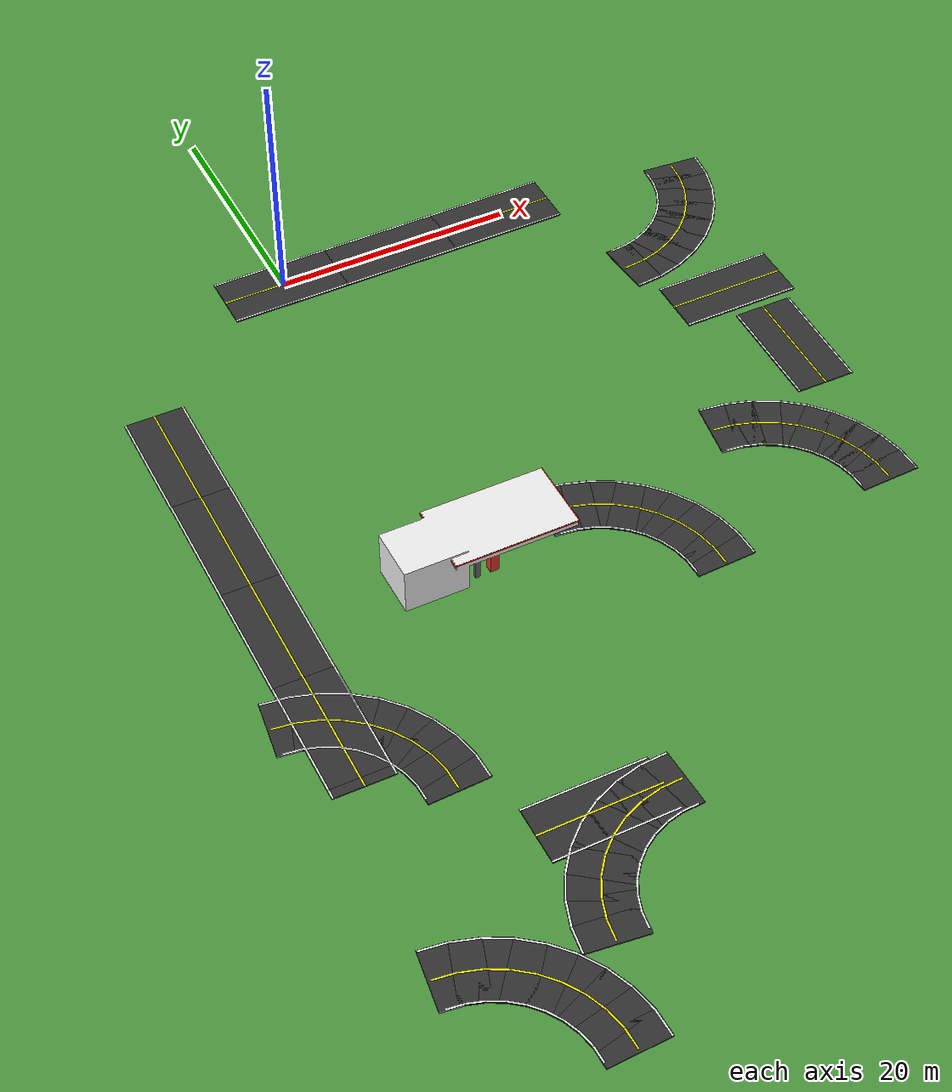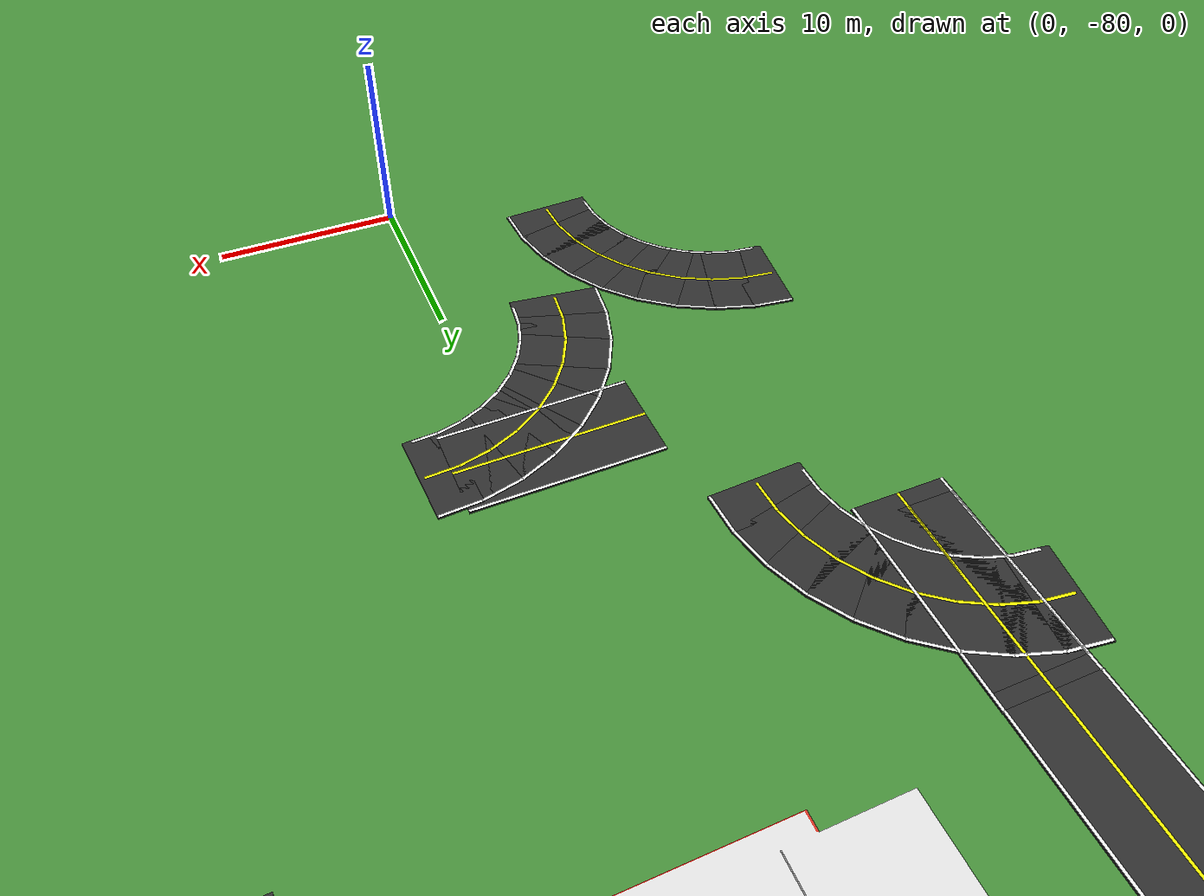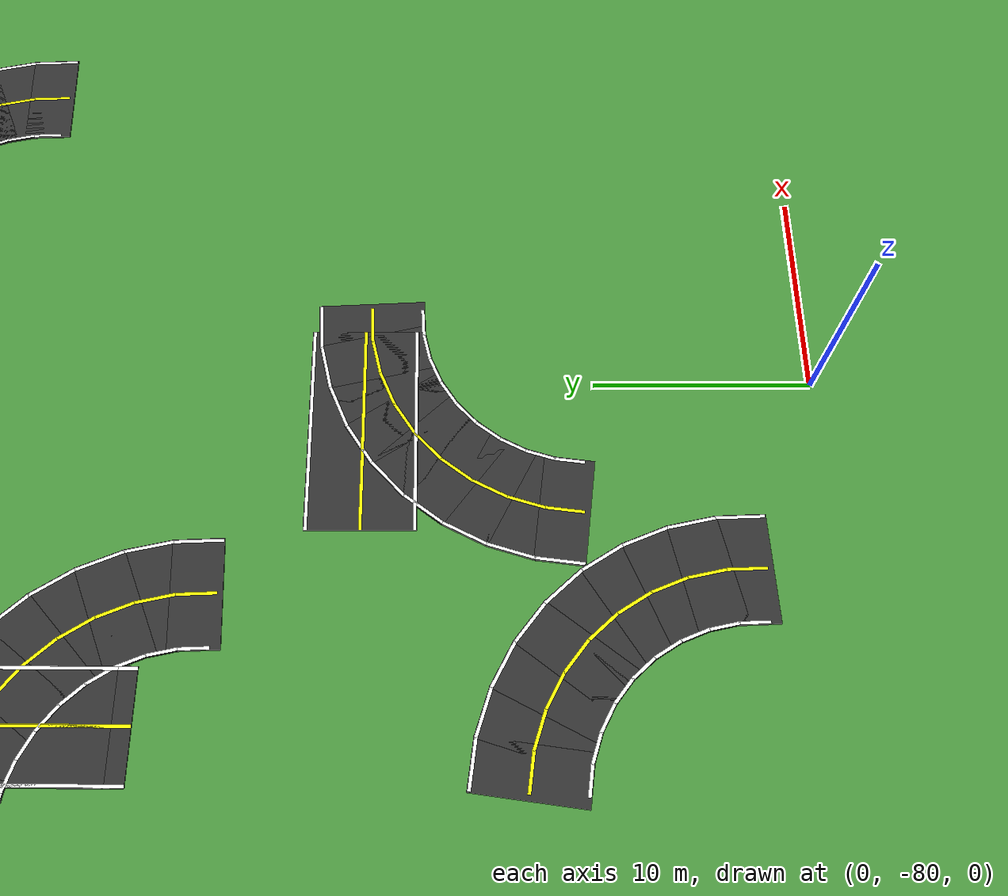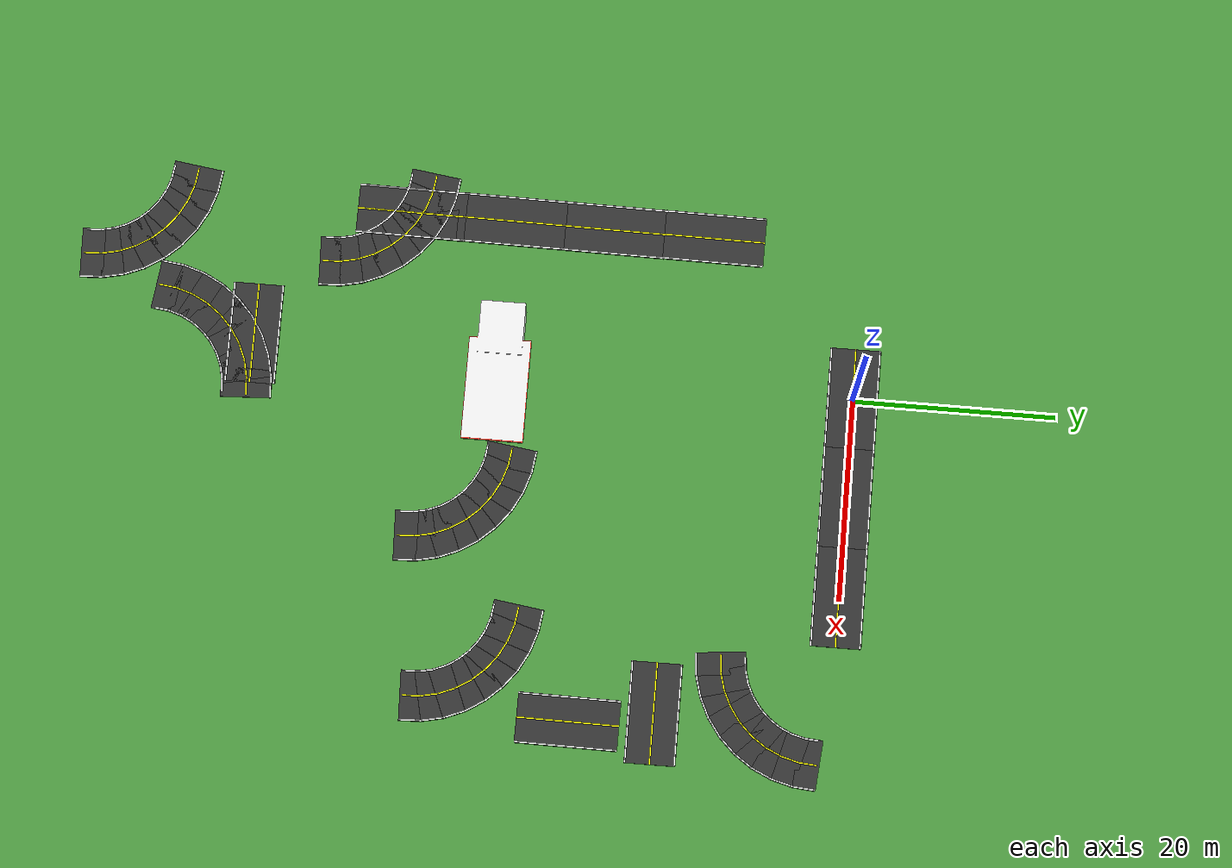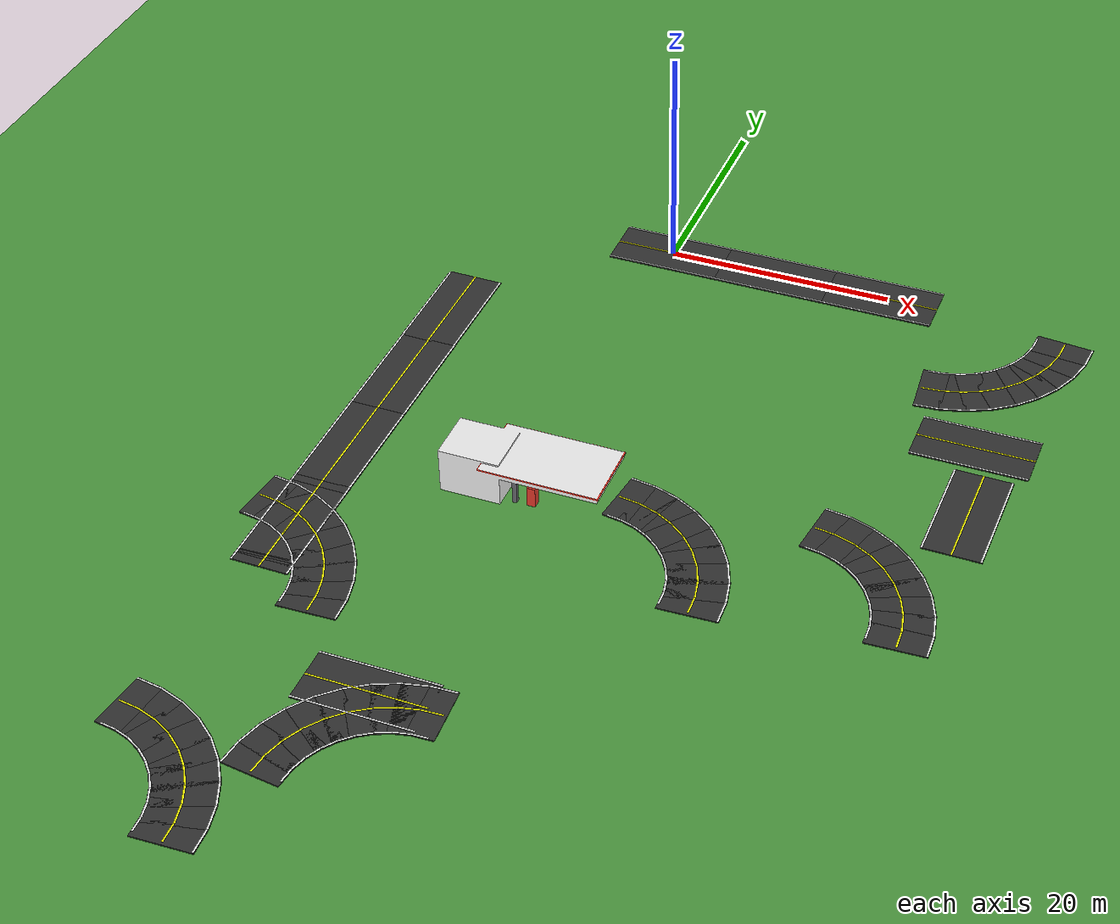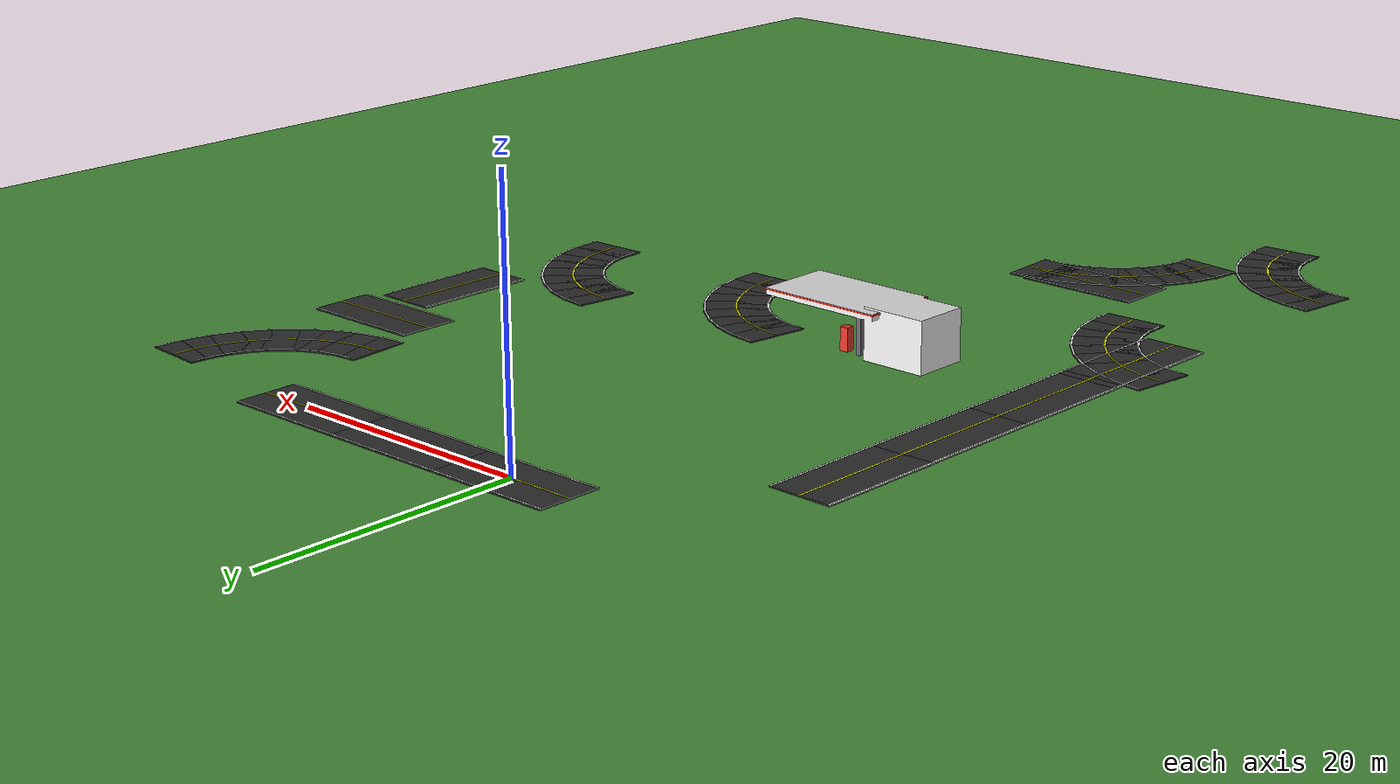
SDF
<?xml version='1.0' encoding='utf-8'?>
<sdf version="1.7">
  <model name="gas_station_2">
    <static>true</static>
    <model name="ground_plane">
      <static>1</static>
      <link name="link">
        <collision name="collision">
          <geometry>
            <plane>
              <normal>0 0 1</normal>
              <size>100 100</size>
            </plane>
          </geometry>
          <surface>
            <contact>
              <collide_bitmask>65535</collide_bitmask>
              <ode />
            </contact>
            <friction>
              <ode>
                <mu>100</mu>
                <mu2>50</mu2>
              </ode>
              <torsional>
                <ode />
              </torsional>
            </friction>
            <bounce />
          </surface>
          <max_contacts>10</max_contacts>
        </collision>
        <visual name="visual">
          <cast_shadows>0</cast_shadows>
          <geometry>
            <plane>
              <normal>0 0 1</normal>
              <size>100 100</size>
            </plane>
          </geometry>
          <material>
            <script>
              <uri>file://media/materials/scripts/gazebo.material</uri>
              <name>Gazebo/Grass</name>
            </script>
          </material>
        </visual>
        <self_collide>0</self_collide>
        <enable_wind>0</enable_wind>
        <kinematic>0</kinematic>
      </link>
    </model>
    <model name="road_straight">
      <static>1</static>
      <link name="link">
        <collision name="collision">
          <geometry>
            <box>
              <size>10 5 0.1</size>
            </box>
          </geometry>
          <max_contacts>10</max_contacts>
          <surface>
            <contact>
              <ode />
            </contact>
            <bounce />
            <friction>
              <torsional>
                <ode />
              </torsional>
              <ode />
            </friction>
          </surface>
        </collision>
        <visual name="visual_surface">
          <geometry>
            <box>
              <size>10 5 0.1</size>
            </box>
          </geometry>
          <material>
            <ambient>0.2 0.2 0.2 1</ambient>
            <diffuse>0.2 0.2 0.2 1</diffuse>
            <specular>0.1 0.1 0.1 1</specular>
          </material>
        </visual>
        <visual name="visual_center_line">
          <pose>0 0 0.051 0 -0 0</pose>
          <geometry>
            <box>
              <size>10 0.15 0.001</size>
            </box>
          </geometry>
          <material>
            <ambient>1 1 0 1</ambient>
            <diffuse>1 1 0 1</diffuse>
          </material>
        </visual>
        <visual name="visual_left_line">
          <pose>0 2.4 0.051 0 -0 0</pose>
          <geometry>
            <box>
              <size>10 0.15 0.001</size>
            </box>
          </geometry>
          <material>
            <ambient>1 1 1 1</ambient>
            <diffuse>1 1 1 1</diffuse>
          </material>
        </visual>
        <visual name="visual_right_line">
          <pose>0 -2.4 0.051 0 -0 0</pose>
          <geometry>
            <box>
              <size>10 0.15 0.001</size>
            </box>
          </geometry>
          <material>
            <ambient>1 1 1 1</ambient>
            <diffuse>1 1 1 1</diffuse>
          </material>
        </visual>
        <self_collide>0</self_collide>
        <enable_wind>0</enable_wind>
        <kinematic>0</kinematic>
      </link>
      <pose>-0.248347 0.000542 0 0 -0 0</pose>
    </model>
    <model name="road_straight_clone">
      <static>1</static>
      <link name="link">
        <collision name="collision">
          <geometry>
            <box>
              <size>10 5 0.1</size>
            </box>
          </geometry>
          <max_contacts>10</max_contacts>
          <surface>
            <contact>
              <ode />
            </contact>
            <bounce />
            <friction>
              <torsional>
                <ode />
              </torsional>
              <ode />
            </friction>
          </surface>
        </collision>
        <visual name="visual_surface">
          <geometry>
            <box>
              <size>10 5 0.1</size>
            </box>
          </geometry>
          <material>
            <ambient>0.2 0.2 0.2 1</ambient>
            <diffuse>0.2 0.2 0.2 1</diffuse>
            <specular>0.1 0.1 0.1 1</specular>
          </material>
        </visual>
        <visual name="visual_center_line">
          <pose>0 0 0.051 0 -0 0</pose>
          <geometry>
            <box>
              <size>10 0.15 0.001</size>
            </box>
          </geometry>
          <material>
            <ambient>1 1 0 1</ambient>
            <diffuse>1 1 0 1</diffuse>
          </material>
        </visual>
        <visual name="visual_left_line">
          <pose>0 2.4 0.051 0 -0 0</pose>
          <geometry>
            <box>
              <size>10 0.15 0.001</size>
            </box>
          </geometry>
          <material>
            <ambient>1 1 1 1</ambient>
            <diffuse>1 1 1 1</diffuse>
          </material>
        </visual>
        <visual name="visual_right_line">
          <pose>0 -2.4 0.051 0 -0 0</pose>
          <geometry>
            <box>
              <size>10 0.15 0.001</size>
            </box>
          </geometry>
          <material>
            <ambient>1 1 1 1</ambient>
            <diffuse>1 1 1 1</diffuse>
          </material>
        </visual>
        <self_collide>0</self_collide>
        <enable_wind>0</enable_wind>
        <kinematic>0</kinematic>
      </link>
      <pose>9.70219 0.000539 0 0 -0 0</pose>
    </model>
    <model name="road_straight_clone_clone">
      <static>1</static>
      <link name="link">
        <collision name="collision">
          <geometry>
            <box>
              <size>10 5 0.1</size>
            </box>
          </geometry>
          <max_contacts>10</max_contacts>
          <surface>
            <contact>
              <ode />
            </contact>
            <bounce />
            <friction>
              <torsional>
                <ode />
              </torsional>
              <ode />
            </friction>
          </surface>
        </collision>
        <visual name="visual_surface">
          <geometry>
            <box>
              <size>10 5 0.1</size>
            </box>
          </geometry>
          <material>
            <ambient>0.2 0.2 0.2 1</ambient>
            <diffuse>0.2 0.2 0.2 1</diffuse>
            <specular>0.1 0.1 0.1 1</specular>
          </material>
        </visual>
        <visual name="visual_center_line">
          <pose>0 0 0.051 0 -0 0</pose>
          <geometry>
            <box>
              <size>10 0.15 0.001</size>
            </box>
          </geometry>
          <material>
            <ambient>1 1 0 1</ambient>
            <diffuse>1 1 0 1</diffuse>
          </material>
        </visual>
        <visual name="visual_left_line">
          <pose>0 2.4 0.051 0 -0 0</pose>
          <geometry>
            <box>
              <size>10 0.15 0.001</size>
            </box>
          </geometry>
          <material>
            <ambient>1 1 1 1</ambient>
            <diffuse>1 1 1 1</diffuse>
          </material>
        </visual>
        <visual name="visual_right_line">
          <pose>0 -2.4 0.051 0 -0 0</pose>
          <geometry>
            <box>
              <size>10 0.15 0.001</size>
            </box>
          </geometry>
          <material>
            <ambient>1 1 1 1</ambient>
            <diffuse>1 1 1 1</diffuse>
          </material>
        </visual>
        <self_collide>0</self_collide>
        <enable_wind>0</enable_wind>
        <kinematic>0</kinematic>
      </link>
      <pose>19.59 0.00396 0 0 -0 0</pose>
    </model>
    <model name="road_curved">
      <static>1</static>
      <link name="link">
        <visual name="visual_segment_0">
          <pose>0.8716 0.0381 0 0 -0 0.0873</pose>
          <geometry>
            <box>
              <size>2.2789 5 0.1</size>
            </box>
          </geometry>
          <material>
            <ambient>0.2 0.2 0.2 1</ambient>
            <diffuse>0.2 0.2 0.2 1</diffuse>
            <specular>0.1 0.1 0.1 1</specular>
          </material>
        </visual>
        <collision name="collision_segment_0">
          <pose>0.8716 0.0381 0 0 -0 0.0873</pose>
          <geometry>
            <box>
              <size>2.2789 5 0.1</size>
            </box>
          </geometry>
          <max_contacts>10</max_contacts>
          <surface>
            <contact>
              <ode />
            </contact>
            <bounce />
            <friction>
              <torsional>
                <ode />
              </torsional>
              <ode />
            </friction>
          </surface>
        </collision>
        <visual name="visual_center_line_0">
          <pose>0.8716 0.0381 0.051 0 -0 0.0873</pose>
          <geometry>
            <box>
              <size>1.7931 0.15 0.001</size>
            </box>
          </geometry>
          <material>
            <ambient>1 1 0 1</ambient>
            <diffuse>1 1 0 1</diffuse>
          </material>
        </visual>
        <visual name="visual_inner_line_0">
          <pose>0.6624 2.4289 0.051 0 -0 0.0873</pose>
          <geometry>
            <box>
              <size>1.3748 0.15 0.001</size>
            </box>
          </geometry>
          <material>
            <ambient>1 1 1 1</ambient>
            <diffuse>1 1 1 1</diffuse>
          </material>
        </visual>
        <visual name="visual_outer_line_0">
          <pose>1.0807 -2.3528 0.051 0 -0 0.0873</pose>
          <geometry>
            <box>
              <size>2.2115 0.15 0.001</size>
            </box>
          </geometry>
          <material>
            <ambient>1 1 1 1</ambient>
            <diffuse>1 1 1 1</diffuse>
          </material>
        </visual>
        <visual name="visual_segment_1">
          <pose>2.5882 0.3407 0 0 -0 0.2618</pose>
          <geometry>
            <box>
              <size>2.2789 5 0.1</size>
            </box>
          </geometry>
          <material>
            <ambient>0.2 0.2 0.2 1</ambient>
            <diffuse>0.2 0.2 0.2 1</diffuse>
            <specular>0.1 0.1 0.1 1</specular>
          </material>
        </visual>
        <collision name="collision_segment_1">
          <pose>2.5882 0.3407 0 0 -0 0.2618</pose>
          <geometry>
            <box>
              <size>2.2789 5 0.1</size>
            </box>
          </geometry>
          <max_contacts>10</max_contacts>
          <surface>
            <contact>
              <ode />
            </contact>
            <bounce />
            <friction>
              <torsional>
                <ode />
              </torsional>
              <ode />
            </friction>
          </surface>
        </collision>
        <visual name="visual_center_line_1">
          <pose>2.5882 0.3407 0.051 0 -0 0.2618</pose>
          <geometry>
            <box>
              <size>1.7931 0.15 0.001</size>
            </box>
          </geometry>
          <material>
            <ambient>1 1 0 1</ambient>
            <diffuse>1 1 0 1</diffuse>
          </material>
        </visual>
        <visual name="visual_inner_line_1">
          <pose>1.967 2.659 0.051 0 -0 0.2618</pose>
          <geometry>
            <box>
              <size>1.3748 0.15 0.001</size>
            </box>
          </geometry>
          <material>
            <ambient>1 1 1 1</ambient>
            <diffuse>1 1 1 1</diffuse>
          </material>
        </visual>
        <visual name="visual_outer_line_1">
          <pose>3.2094 -1.9775 0.051 0 -0 0.2618</pose>
          <geometry>
            <box>
              <size>2.2115 0.15 0.001</size>
            </box>
          </geometry>
          <material>
            <ambient>1 1 1 1</ambient>
            <diffuse>1 1 1 1</diffuse>
          </material>
        </visual>
        <visual name="visual_segment_2">
          <pose>4.2262 0.9369 0 0 -0 0.4363</pose>
          <geometry>
            <box>
              <size>2.2789 5 0.1</size>
            </box>
          </geometry>
          <material>
            <ambient>0.2 0.2 0.2 1</ambient>
            <diffuse>0.2 0.2 0.2 1</diffuse>
            <specular>0.1 0.1 0.1 1</specular>
          </material>
        </visual>
        <collision name="collision_segment_2">
          <pose>4.2262 0.9369 0 0 -0 0.4363</pose>
          <geometry>
            <box>
              <size>2.2789 5 0.1</size>
            </box>
          </geometry>
          <max_contacts>10</max_contacts>
          <surface>
            <contact>
              <ode />
            </contact>
            <bounce />
            <friction>
              <torsional>
                <ode />
              </torsional>
              <ode />
            </friction>
          </surface>
        </collision>
        <visual name="visual_center_line_2">
          <pose>4.2262 0.9369 0.051 0 -0 0.4363</pose>
          <geometry>
            <box>
              <size>1.7931 0.15 0.001</size>
            </box>
          </geometry>
          <material>
            <ambient>1 1 0 1</ambient>
            <diffuse>1 1 0 1</diffuse>
          </material>
        </visual>
        <visual name="visual_inner_line_2">
          <pose>3.2119 3.1121 0.051 0 -0 0.4363</pose>
          <geometry>
            <box>
              <size>1.3748 0.15 0.001</size>
            </box>
          </geometry>
          <material>
            <ambient>1 1 1 1</ambient>
            <diffuse>1 1 1 1</diffuse>
          </material>
        </visual>
        <visual name="visual_outer_line_2">
          <pose>5.2405 -1.2382 0.051 0 -0 0.4363</pose>
          <geometry>
            <box>
              <size>2.2115 0.15 0.001</size>
            </box>
          </geometry>
          <material>
            <ambient>1 1 1 1</ambient>
            <diffuse>1 1 1 1</diffuse>
          </material>
        </visual>
        <visual name="visual_segment_3">
          <pose>5.7358 1.8085 0 0 -0 0.6109</pose>
          <geometry>
            <box>
              <size>2.2789 5 0.1</size>
            </box>
          </geometry>
          <material>
            <ambient>0.2 0.2 0.2 1</ambient>
            <diffuse>0.2 0.2 0.2 1</diffuse>
            <specular>0.1 0.1 0.1 1</specular>
          </material>
        </visual>
        <collision name="collision_segment_3">
          <pose>5.7358 1.8085 0 0 -0 0.6109</pose>
          <geometry>
            <box>
              <size>2.2789 5 0.1</size>
            </box>
          </geometry>
          <max_contacts>10</max_contacts>
          <surface>
            <contact>
              <ode />
            </contact>
            <bounce />
            <friction>
              <torsional>
                <ode />
              </torsional>
              <ode />
            </friction>
          </surface>
        </collision>
        <visual name="visual_center_line_3">
          <pose>5.7358 1.8085 0.051 0 -0 0.6109</pose>
          <geometry>
            <box>
              <size>1.7931 0.15 0.001</size>
            </box>
          </geometry>
          <material>
            <ambient>1 1 0 1</ambient>
            <diffuse>1 1 0 1</diffuse>
          </material>
        </visual>
        <visual name="visual_inner_line_3">
          <pose>4.3592 3.7744 0.051 0 -0 0.6109</pose>
          <geometry>
            <box>
              <size>1.3748 0.15 0.001</size>
            </box>
          </geometry>
          <material>
            <ambient>1 1 1 1</ambient>
            <diffuse>1 1 1 1</diffuse>
          </material>
        </visual>
        <visual name="visual_outer_line_3">
          <pose>7.1123 -0.1575 0.051 0 -0 0.6109</pose>
          <geometry>
            <box>
              <size>2.2115 0.15 0.001</size>
            </box>
          </geometry>
          <material>
            <ambient>1 1 1 1</ambient>
            <diffuse>1 1 1 1</diffuse>
          </material>
        </visual>
        <visual name="visual_segment_4">
          <pose>7.0711 2.9289 0 0 -0 0.7854</pose>
          <geometry>
            <box>
              <size>2.2789 5 0.1</size>
            </box>
          </geometry>
          <material>
            <ambient>0.2 0.2 0.2 1</ambient>
            <diffuse>0.2 0.2 0.2 1</diffuse>
            <specular>0.1 0.1 0.1 1</specular>
          </material>
        </visual>
        <collision name="collision_segment_4">
          <pose>7.0711 2.9289 0 0 -0 0.7854</pose>
          <geometry>
            <box>
              <size>2.2789 5 0.1</size>
            </box>
          </geometry>
          <max_contacts>10</max_contacts>
          <surface>
            <contact>
              <ode />
            </contact>
            <bounce />
            <friction>
              <torsional>
                <ode />
              </torsional>
              <ode />
            </friction>
          </surface>
        </collision>
        <visual name="visual_center_line_4">
          <pose>7.0711 2.9289 0.051 0 -0 0.7854</pose>
          <geometry>
            <box>
              <size>1.7931 0.15 0.001</size>
            </box>
          </geometry>
          <material>
            <ambient>1 1 0 1</ambient>
            <diffuse>1 1 0 1</diffuse>
          </material>
        </visual>
        <visual name="visual_inner_line_4">
          <pose>5.374 4.626 0.051 0 -0 0.7854</pose>
          <geometry>
            <box>
              <size>1.3748 0.15 0.001</size>
            </box>
          </geometry>
          <material>
            <ambient>1 1 1 1</ambient>
            <diffuse>1 1 1 1</diffuse>
          </material>
        </visual>
        <visual name="visual_outer_line_4">
          <pose>8.7681 1.2319 0.051 0 -0 0.7854</pose>
          <geometry>
            <box>
              <size>2.2115 0.15 0.001</size>
            </box>
          </geometry>
          <material>
            <ambient>1 1 1 1</ambient>
            <diffuse>1 1 1 1</diffuse>
          </material>
        </visual>
        <visual name="visual_segment_5">
          <pose>8.1915 4.2642 0 0 -0 0.9599</pose>
          <geometry>
            <box>
              <size>2.2789 5 0.1</size>
            </box>
          </geometry>
          <material>
            <ambient>0.2 0.2 0.2 1</ambient>
            <diffuse>0.2 0.2 0.2 1</diffuse>
            <specular>0.1 0.1 0.1 1</specular>
          </material>
        </visual>
        <collision name="collision_segment_5">
          <pose>8.1915 4.2642 0 0 -0 0.9599</pose>
          <geometry>
            <box>
              <size>2.2789 5 0.1</size>
            </box>
          </geometry>
          <max_contacts>10</max_contacts>
          <surface>
            <contact>
              <ode />
            </contact>
            <bounce />
            <friction>
              <torsional>
                <ode />
              </torsional>
              <ode />
            </friction>
          </surface>
        </collision>
        <visual name="visual_center_line_5">
          <pose>8.1915 4.2642 0.051 0 -0 0.9599</pose>
          <geometry>
            <box>
              <size>1.7931 0.15 0.001</size>
            </box>
          </geometry>
          <material>
            <ambient>1 1 0 1</ambient>
            <diffuse>1 1 0 1</diffuse>
          </material>
        </visual>
        <visual name="visual_inner_line_5">
          <pose>6.2256 5.6408 0.051 0 -0 0.9599</pose>
          <geometry>
            <box>
              <size>1.3748 0.15 0.001</size>
            </box>
          </geometry>
          <material>
            <ambient>1 1 1 1</ambient>
            <diffuse>1 1 1 1</diffuse>
          </material>
        </visual>
        <visual name="visual_outer_line_5">
          <pose>10.1575 2.8877 0.051 0 -0 0.9599</pose>
          <geometry>
            <box>
              <size>2.2115 0.15 0.001</size>
            </box>
          </geometry>
          <material>
            <ambient>1 1 1 1</ambient>
            <diffuse>1 1 1 1</diffuse>
          </material>
        </visual>
        <visual name="visual_segment_6">
          <pose>9.0631 5.7738 0 0 -0 1.1345</pose>
          <geometry>
            <box>
              <size>2.2789 5 0.1</size>
            </box>
          </geometry>
          <material>
            <ambient>0.2 0.2 0.2 1</ambient>
            <diffuse>0.2 0.2 0.2 1</diffuse>
            <specular>0.1 0.1 0.1 1</specular>
          </material>
        </visual>
        <collision name="collision_segment_6">
          <pose>9.0631 5.7738 0 0 -0 1.1345</pose>
          <geometry>
            <box>
              <size>2.2789 5 0.1</size>
            </box>
          </geometry>
          <max_contacts>10</max_contacts>
          <surface>
            <contact>
              <ode />
            </contact>
            <bounce />
            <friction>
              <torsional>
                <ode />
              </torsional>
              <ode />
            </friction>
          </surface>
        </collision>
        <visual name="visual_center_line_6">
          <pose>9.0631 5.7738 0.051 0 -0 1.1345</pose>
          <geometry>
            <box>
              <size>1.7931 0.15 0.001</size>
            </box>
          </geometry>
          <material>
            <ambient>1 1 0 1</ambient>
            <diffuse>1 1 0 1</diffuse>
          </material>
        </visual>
        <visual name="visual_inner_line_6">
          <pose>6.8879 6.7881 0.051 0 -0 1.1345</pose>
          <geometry>
            <box>
              <size>1.3748 0.15 0.001</size>
            </box>
          </geometry>
          <material>
            <ambient>1 1 1 1</ambient>
            <diffuse>1 1 1 1</diffuse>
          </material>
        </visual>
        <visual name="visual_outer_line_6">
          <pose>11.2382 4.7595 0.051 0 -0 1.1345</pose>
          <geometry>
            <box>
              <size>2.2115 0.15 0.001</size>
            </box>
          </geometry>
          <material>
            <ambient>1 1 1 1</ambient>
            <diffuse>1 1 1 1</diffuse>
          </material>
        </visual>
        <visual name="visual_segment_7">
          <pose>9.6593 7.4118 0 0 -0 1.309</pose>
          <geometry>
            <box>
              <size>2.2789 5 0.1</size>
            </box>
          </geometry>
          <material>
            <ambient>0.2 0.2 0.2 1</ambient>
            <diffuse>0.2 0.2 0.2 1</diffuse>
            <specular>0.1 0.1 0.1 1</specular>
          </material>
        </visual>
        <collision name="collision_segment_7">
          <pose>9.6593 7.4118 0 0 -0 1.309</pose>
          <geometry>
            <box>
              <size>2.2789 5 0.1</size>
            </box>
          </geometry>
          <max_contacts>10</max_contacts>
          <surface>
            <contact>
              <ode />
            </contact>
            <bounce />
            <friction>
              <torsional>
                <ode />
              </torsional>
              <ode />
            </friction>
          </surface>
        </collision>
        <visual name="visual_center_line_7">
          <pose>9.6593 7.4118 0.051 0 -0 1.309</pose>
          <geometry>
            <box>
              <size>1.7931 0.15 0.001</size>
            </box>
          </geometry>
          <material>
            <ambient>1 1 0 1</ambient>
            <diffuse>1 1 0 1</diffuse>
          </material>
        </visual>
        <visual name="visual_inner_line_7">
          <pose>7.341 8.033 0.051 0 -0 1.309</pose>
          <geometry>
            <box>
              <size>1.3748 0.15 0.001</size>
            </box>
          </geometry>
          <material>
            <ambient>1 1 1 1</ambient>
            <diffuse>1 1 1 1</diffuse>
          </material>
        </visual>
        <visual name="visual_outer_line_7">
          <pose>11.9775 6.7906 0.051 0 -0 1.309</pose>
          <geometry>
            <box>
              <size>2.2115 0.15 0.001</size>
            </box>
          </geometry>
          <material>
            <ambient>1 1 1 1</ambient>
            <diffuse>1 1 1 1</diffuse>
          </material>
        </visual>
        <visual name="visual_segment_8">
          <pose>9.9619 9.1284 0 0 -0 1.4835</pose>
          <geometry>
            <box>
              <size>2.2789 5 0.1</size>
            </box>
          </geometry>
          <material>
            <ambient>0.2 0.2 0.2 1</ambient>
            <diffuse>0.2 0.2 0.2 1</diffuse>
            <specular>0.1 0.1 0.1 1</specular>
          </material>
        </visual>
        <collision name="collision_segment_8">
          <pose>9.9619 9.1284 0 0 -0 1.4835</pose>
          <geometry>
            <box>
              <size>2.2789 5 0.1</size>
            </box>
          </geometry>
          <max_contacts>10</max_contacts>
          <surface>
            <contact>
              <ode />
            </contact>
            <bounce />
            <friction>
              <torsional>
                <ode />
              </torsional>
              <ode />
            </friction>
          </surface>
        </collision>
        <visual name="visual_center_line_8">
          <pose>9.9619 9.1284 0.051 0 -0 1.4835</pose>
          <geometry>
            <box>
              <size>1.7931 0.15 0.001</size>
            </box>
          </geometry>
          <material>
            <ambient>1 1 0 1</ambient>
            <diffuse>1 1 0 1</diffuse>
          </material>
        </visual>
        <visual name="visual_inner_line_8">
          <pose>7.5711 9.3376 0.051 0 -0 1.4835</pose>
          <geometry>
            <box>
              <size>1.3748 0.15 0.001</size>
            </box>
          </geometry>
          <material>
            <ambient>1 1 1 1</ambient>
            <diffuse>1 1 1 1</diffuse>
          </material>
        </visual>
        <visual name="visual_outer_line_8">
          <pose>12.3528 8.9193 0.051 0 -0 1.4835</pose>
          <geometry>
            <box>
              <size>2.2115 0.15 0.001</size>
            </box>
          </geometry>
          <material>
            <ambient>1 1 1 1</ambient>
            <diffuse>1 1 1 1</diffuse>
          </material>
        </visual>
        <self_collide>0</self_collide>
        <enable_wind>0</enable_wind>
        <kinematic>0</kinematic>
      </link>
      <pose>26.2003 -11.0275 0 0 -0 0</pose>
    </model>
    <model name="road_straight_clone_clone_clone">
      <static>1</static>
      <link name="link">
        <collision name="collision">
          <geometry>
            <box>
              <size>10 5 0.1</size>
            </box>
          </geometry>
          <max_contacts>10</max_contacts>
          <surface>
            <contact>
              <ode />
            </contact>
            <bounce />
            <friction>
              <torsional>
                <ode />
              </torsional>
              <ode />
            </friction>
          </surface>
        </collision>
        <visual name="visual_surface">
          <geometry>
            <box>
              <size>10 5 0.1</size>
            </box>
          </geometry>
          <material>
            <ambient>0.2 0.2 0.2 1</ambient>
            <diffuse>0.2 0.2 0.2 1</diffuse>
            <specular>0.1 0.1 0.1 1</specular>
          </material>
        </visual>
        <visual name="visual_center_line">
          <pose>0 0 0.051 0 -0 0</pose>
          <geometry>
            <box>
              <size>10 0.15 0.001</size>
            </box>
          </geometry>
          <material>
            <ambient>1 1 0 1</ambient>
            <diffuse>1 1 0 1</diffuse>
          </material>
        </visual>
        <visual name="visual_left_line">
          <pose>0 2.4 0.051 0 -0 0</pose>
          <geometry>
            <box>
              <size>10 0.15 0.001</size>
            </box>
          </geometry>
          <material>
            <ambient>1 1 1 1</ambient>
            <diffuse>1 1 1 1</diffuse>
          </material>
        </visual>
        <visual name="visual_right_line">
          <pose>0 -2.4 0.051 0 -0 0</pose>
          <geometry>
            <box>
              <size>10 0.15 0.001</size>
            </box>
          </geometry>
          <material>
            <ambient>1 1 1 1</ambient>
            <diffuse>1 1 1 1</diffuse>
          </material>
        </visual>
        <self_collide>0</self_collide>
        <enable_wind>0</enable_wind>
        <kinematic>0</kinematic>
      </link>
      <pose>32.4471 -17.1551 0 0 -0 0</pose>
    </model>
    <model name="road_straight_clone_clone_clone_clone">
      <static>1</static>
      <link name="link">
        <collision name="collision">
          <geometry>
            <box>
              <size>10 5 0.1</size>
            </box>
          </geometry>
          <max_contacts>10</max_contacts>
          <surface>
            <contact>
              <ode />
            </contact>
            <bounce />
            <friction>
              <torsional>
                <ode />
              </torsional>
              <ode />
            </friction>
          </surface>
        </collision>
        <visual name="visual_surface">
          <geometry>
            <box>
              <size>10 5 0.1</size>
            </box>
          </geometry>
          <material>
            <ambient>0.2 0.2 0.2 1</ambient>
            <diffuse>0.2 0.2 0.2 1</diffuse>
            <specular>0.1 0.1 0.1 1</specular>
          </material>
        </visual>
        <visual name="visual_center_line">
          <pose>0 0 0.051 0 -0 0</pose>
          <geometry>
            <box>
              <size>10 0.15 0.001</size>
            </box>
          </geometry>
          <material>
            <ambient>1 1 0 1</ambient>
            <diffuse>1 1 0 1</diffuse>
          </material>
        </visual>
        <visual name="visual_left_line">
          <pose>0 2.4 0.051 0 -0 0</pose>
          <geometry>
            <box>
              <size>10 0.15 0.001</size>
            </box>
          </geometry>
          <material>
            <ambient>1 1 1 1</ambient>
            <diffuse>1 1 1 1</diffuse>
          </material>
        </visual>
        <visual name="visual_right_line">
          <pose>0 -2.4 0.051 0 -0 0</pose>
          <geometry>
            <box>
              <size>10 0.15 0.001</size>
            </box>
          </geometry>
          <material>
            <ambient>1 1 1 1</ambient>
            <diffuse>1 1 1 1</diffuse>
          </material>
        </visual>
        <self_collide>0</self_collide>
        <enable_wind>0</enable_wind>
        <kinematic>0</kinematic>
      </link>
      <pose>33.9162 -25.3829 0 0 -0 1.56099</pose>
    </model>
    <model name="road_curved_clone">
      <static>1</static>
      <link name="link">
        <visual name="visual_segment_0">
          <pose>0.8716 0.0381 0 0 -0 0.0873</pose>
          <geometry>
            <box>
              <size>2.2789 5 0.1</size>
            </box>
          </geometry>
          <material>
            <ambient>0.2 0.2 0.2 1</ambient>
            <diffuse>0.2 0.2 0.2 1</diffuse>
            <specular>0.1 0.1 0.1 1</specular>
          </material>
        </visual>
        <collision name="collision_segment_0">
          <pose>0.8716 0.0381 0 0 -0 0.0873</pose>
          <geometry>
            <box>
              <size>2.2789 5 0.1</size>
            </box>
          </geometry>
          <max_contacts>10</max_contacts>
          <surface>
            <contact>
              <ode />
            </contact>
            <bounce />
            <friction>
              <torsional>
                <ode />
              </torsional>
              <ode />
            </friction>
          </surface>
        </collision>
        <visual name="visual_center_line_0">
          <pose>0.8716 0.0381 0.051 0 -0 0.0873</pose>
          <geometry>
            <box>
              <size>1.7931 0.15 0.001</size>
            </box>
          </geometry>
          <material>
            <ambient>1 1 0 1</ambient>
            <diffuse>1 1 0 1</diffuse>
          </material>
        </visual>
        <visual name="visual_inner_line_0">
          <pose>0.6624 2.4289 0.051 0 -0 0.0873</pose>
          <geometry>
            <box>
              <size>1.3748 0.15 0.001</size>
            </box>
          </geometry>
          <material>
            <ambient>1 1 1 1</ambient>
            <diffuse>1 1 1 1</diffuse>
          </material>
        </visual>
        <visual name="visual_outer_line_0">
          <pose>1.0807 -2.3528 0.051 0 -0 0.0873</pose>
          <geometry>
            <box>
              <size>2.2115 0.15 0.001</size>
            </box>
          </geometry>
          <material>
            <ambient>1 1 1 1</ambient>
            <diffuse>1 1 1 1</diffuse>
          </material>
        </visual>
        <visual name="visual_segment_1">
          <pose>2.5882 0.3407 0 0 -0 0.2618</pose>
          <geometry>
            <box>
              <size>2.2789 5 0.1</size>
            </box>
          </geometry>
          <material>
            <ambient>0.2 0.2 0.2 1</ambient>
            <diffuse>0.2 0.2 0.2 1</diffuse>
            <specular>0.1 0.1 0.1 1</specular>
          </material>
        </visual>
        <collision name="collision_segment_1">
          <pose>2.5882 0.3407 0 0 -0 0.2618</pose>
          <geometry>
            <box>
              <size>2.2789 5 0.1</size>
            </box>
          </geometry>
          <max_contacts>10</max_contacts>
          <surface>
            <contact>
              <ode />
            </contact>
            <bounce />
            <friction>
              <torsional>
                <ode />
              </torsional>
              <ode />
            </friction>
          </surface>
        </collision>
        <visual name="visual_center_line_1">
          <pose>2.5882 0.3407 0.051 0 -0 0.2618</pose>
          <geometry>
            <box>
              <size>1.7931 0.15 0.001</size>
            </box>
          </geometry>
          <material>
            <ambient>1 1 0 1</ambient>
            <diffuse>1 1 0 1</diffuse>
          </material>
        </visual>
        <visual name="visual_inner_line_1">
          <pose>1.967 2.659 0.051 0 -0 0.2618</pose>
          <geometry>
            <box>
              <size>1.3748 0.15 0.001</size>
            </box>
          </geometry>
          <material>
            <ambient>1 1 1 1</ambient>
            <diffuse>1 1 1 1</diffuse>
          </material>
        </visual>
        <visual name="visual_outer_line_1">
          <pose>3.2094 -1.9775 0.051 0 -0 0.2618</pose>
          <geometry>
            <box>
              <size>2.2115 0.15 0.001</size>
            </box>
          </geometry>
          <material>
            <ambient>1 1 1 1</ambient>
            <diffuse>1 1 1 1</diffuse>
          </material>
        </visual>
        <visual name="visual_segment_2">
          <pose>4.2262 0.9369 0 0 -0 0.4363</pose>
          <geometry>
            <box>
              <size>2.2789 5 0.1</size>
            </box>
          </geometry>
          <material>
            <ambient>0.2 0.2 0.2 1</ambient>
            <diffuse>0.2 0.2 0.2 1</diffuse>
            <specular>0.1 0.1 0.1 1</specular>
          </material>
        </visual>
        <collision name="collision_segment_2">
          <pose>4.2262 0.9369 0 0 -0 0.4363</pose>
          <geometry>
            <box>
              <size>2.2789 5 0.1</size>
            </box>
          </geometry>
          <max_contacts>10</max_contacts>
          <surface>
            <contact>
              <ode />
            </contact>
            <bounce />
            <friction>
              <torsional>
                <ode />
              </torsional>
              <ode />
            </friction>
          </surface>
        </collision>
        <visual name="visual_center_line_2">
          <pose>4.2262 0.9369 0.051 0 -0 0.4363</pose>
          <geometry>
            <box>
              <size>1.7931 0.15 0.001</size>
            </box>
          </geometry>
          <material>
            <ambient>1 1 0 1</ambient>
            <diffuse>1 1 0 1</diffuse>
          </material>
        </visual>
        <visual name="visual_inner_line_2">
          <pose>3.2119 3.1121 0.051 0 -0 0.4363</pose>
          <geometry>
            <box>
              <size>1.3748 0.15 0.001</size>
            </box>
          </geometry>
          <material>
            <ambient>1 1 1 1</ambient>
            <diffuse>1 1 1 1</diffuse>
          </material>
        </visual>
        <visual name="visual_outer_line_2">
          <pose>5.2405 -1.2382 0.051 0 -0 0.4363</pose>
          <geometry>
            <box>
              <size>2.2115 0.15 0.001</size>
            </box>
          </geometry>
          <material>
            <ambient>1 1 1 1</ambient>
            <diffuse>1 1 1 1</diffuse>
          </material>
        </visual>
        <visual name="visual_segment_3">
          <pose>5.7358 1.8085 0 0 -0 0.6109</pose>
          <geometry>
            <box>
              <size>2.2789 5 0.1</size>
            </box>
          </geometry>
          <material>
            <ambient>0.2 0.2 0.2 1</ambient>
            <diffuse>0.2 0.2 0.2 1</diffuse>
            <specular>0.1 0.1 0.1 1</specular>
          </material>
        </visual>
        <collision name="collision_segment_3">
          <pose>5.7358 1.8085 0 0 -0 0.6109</pose>
          <geometry>
            <box>
              <size>2.2789 5 0.1</size>
            </box>
          </geometry>
          <max_contacts>10</max_contacts>
          <surface>
            <contact>
              <ode />
            </contact>
            <bounce />
            <friction>
              <torsional>
                <ode />
              </torsional>
              <ode />
            </friction>
          </surface>
        </collision>
        <visual name="visual_center_line_3">
          <pose>5.7358 1.8085 0.051 0 -0 0.6109</pose>
          <geometry>
            <box>
              <size>1.7931 0.15 0.001</size>
            </box>
          </geometry>
          <material>
            <ambient>1 1 0 1</ambient>
            <diffuse>1 1 0 1</diffuse>
          </material>
        </visual>
        <visual name="visual_inner_line_3">
          <pose>4.3592 3.7744 0.051 0 -0 0.6109</pose>
          <geometry>
            <box>
              <size>1.3748 0.15 0.001</size>
            </box>
          </geometry>
          <material>
            <ambient>1 1 1 1</ambient>
            <diffuse>1 1 1 1</diffuse>
          </material>
        </visual>
        <visual name="visual_outer_line_3">
          <pose>7.1123 -0.1575 0.051 0 -0 0.6109</pose>
          <geometry>
            <box>
              <size>2.2115 0.15 0.001</size>
            </box>
          </geometry>
          <material>
            <ambient>1 1 1 1</ambient>
            <diffuse>1 1 1 1</diffuse>
          </material>
        </visual>
        <visual name="visual_segment_4">
          <pose>7.0711 2.9289 0 0 -0 0.7854</pose>
          <geometry>
            <box>
              <size>2.2789 5 0.1</size>
            </box>
          </geometry>
          <material>
            <ambient>0.2 0.2 0.2 1</ambient>
            <diffuse>0.2 0.2 0.2 1</diffuse>
            <specular>0.1 0.1 0.1 1</specular>
          </material>
        </visual>
        <collision name="collision_segment_4">
          <pose>7.0711 2.9289 0 0 -0 0.7854</pose>
          <geometry>
            <box>
              <size>2.2789 5 0.1</size>
            </box>
          </geometry>
          <max_contacts>10</max_contacts>
          <surface>
            <contact>
              <ode />
            </contact>
            <bounce />
            <friction>
              <torsional>
                <ode />
              </torsional>
              <ode />
            </friction>
          </surface>
        </collision>
        <visual name="visual_center_line_4">
          <pose>7.0711 2.9289 0.051 0 -0 0.7854</pose>
          <geometry>
            <box>
              <size>1.7931 0.15 0.001</size>
            </box>
          </geometry>
          <material>
            <ambient>1 1 0 1</ambient>
            <diffuse>1 1 0 1</diffuse>
          </material>
        </visual>
        <visual name="visual_inner_line_4">
          <pose>5.374 4.626 0.051 0 -0 0.7854</pose>
          <geometry>
            <box>
              <size>1.3748 0.15 0.001</size>
            </box>
          </geometry>
          <material>
            <ambient>1 1 1 1</ambient>
            <diffuse>1 1 1 1</diffuse>
          </material>
        </visual>
        <visual name="visual_outer_line_4">
          <pose>8.7681 1.2319 0.051 0 -0 0.7854</pose>
          <geometry>
            <box>
              <size>2.2115 0.15 0.001</size>
            </box>
          </geometry>
          <material>
            <ambient>1 1 1 1</ambient>
            <diffuse>1 1 1 1</diffuse>
          </material>
        </visual>
        <visual name="visual_segment_5">
          <pose>8.1915 4.2642 0 0 -0 0.9599</pose>
          <geometry>
            <box>
              <size>2.2789 5 0.1</size>
            </box>
          </geometry>
          <material>
            <ambient>0.2 0.2 0.2 1</ambient>
            <diffuse>0.2 0.2 0.2 1</diffuse>
            <specular>0.1 0.1 0.1 1</specular>
          </material>
        </visual>
        <collision name="collision_segment_5">
          <pose>8.1915 4.2642 0 0 -0 0.9599</pose>
          <geometry>
            <box>
              <size>2.2789 5 0.1</size>
            </box>
          </geometry>
          <max_contacts>10</max_contacts>
          <surface>
            <contact>
              <ode />
            </contact>
            <bounce />
            <friction>
              <torsional>
                <ode />
              </torsional>
              <ode />
            </friction>
          </surface>
        </collision>
        <visual name="visual_center_line_5">
          <pose>8.1915 4.2642 0.051 0 -0 0.9599</pose>
          <geometry>
            <box>
              <size>1.7931 0.15 0.001</size>
            </box>
          </geometry>
          <material>
            <ambient>1 1 0 1</ambient>
            <diffuse>1 1 0 1</diffuse>
          </material>
        </visual>
        <visual name="visual_inner_line_5">
          <pose>6.2256 5.6408 0.051 0 -0 0.9599</pose>
          <geometry>
            <box>
              <size>1.3748 0.15 0.001</size>
            </box>
          </geometry>
          <material>
            <ambient>1 1 1 1</ambient>
            <diffuse>1 1 1 1</diffuse>
          </material>
        </visual>
        <visual name="visual_outer_line_5">
          <pose>10.1575 2.8877 0.051 0 -0 0.9599</pose>
          <geometry>
            <box>
              <size>2.2115 0.15 0.001</size>
            </box>
          </geometry>
          <material>
            <ambient>1 1 1 1</ambient>
            <diffuse>1 1 1 1</diffuse>
          </material>
        </visual>
        <visual name="visual_segment_6">
          <pose>9.0631 5.7738 0 0 -0 1.1345</pose>
          <geometry>
            <box>
              <size>2.2789 5 0.1</size>
            </box>
          </geometry>
          <material>
            <ambient>0.2 0.2 0.2 1</ambient>
            <diffuse>0.2 0.2 0.2 1</diffuse>
            <specular>0.1 0.1 0.1 1</specular>
          </material>
        </visual>
        <collision name="collision_segment_6">
          <pose>9.0631 5.7738 0 0 -0 1.1345</pose>
          <geometry>
            <box>
              <size>2.2789 5 0.1</size>
            </box>
          </geometry>
          <max_contacts>10</max_contacts>
          <surface>
            <contact>
              <ode />
            </contact>
            <bounce />
            <friction>
              <torsional>
                <ode />
              </torsional>
              <ode />
            </friction>
          </surface>
        </collision>
        <visual name="visual_center_line_6">
          <pose>9.0631 5.7738 0.051 0 -0 1.1345</pose>
          <geometry>
            <box>
              <size>1.7931 0.15 0.001</size>
            </box>
          </geometry>
          <material>
            <ambient>1 1 0 1</ambient>
            <diffuse>1 1 0 1</diffuse>
          </material>
        </visual>
        <visual name="visual_inner_line_6">
          <pose>6.8879 6.7881 0.051 0 -0 1.1345</pose>
          <geometry>
            <box>
              <size>1.3748 0.15 0.001</size>
            </box>
          </geometry>
          <material>
            <ambient>1 1 1 1</ambient>
            <diffuse>1 1 1 1</diffuse>
          </material>
        </visual>
        <visual name="visual_outer_line_6">
          <pose>11.2382 4.7595 0.051 0 -0 1.1345</pose>
          <geometry>
            <box>
              <size>2.2115 0.15 0.001</size>
            </box>
          </geometry>
          <material>
            <ambient>1 1 1 1</ambient>
            <diffuse>1 1 1 1</diffuse>
          </material>
        </visual>
        <visual name="visual_segment_7">
          <pose>9.6593 7.4118 0 0 -0 1.309</pose>
          <geometry>
            <box>
              <size>2.2789 5 0.1</size>
            </box>
          </geometry>
          <material>
            <ambient>0.2 0.2 0.2 1</ambient>
            <diffuse>0.2 0.2 0.2 1</diffuse>
            <specular>0.1 0.1 0.1 1</specular>
          </material>
        </visual>
        <collision name="collision_segment_7">
          <pose>9.6593 7.4118 0 0 -0 1.309</pose>
          <geometry>
            <box>
              <size>2.2789 5 0.1</size>
            </box>
          </geometry>
          <max_contacts>10</max_contacts>
          <surface>
            <contact>
              <ode />
            </contact>
            <bounce />
            <friction>
              <torsional>
                <ode />
              </torsional>
              <ode />
            </friction>
          </surface>
        </collision>
        <visual name="visual_center_line_7">
          <pose>9.6593 7.4118 0.051 0 -0 1.309</pose>
          <geometry>
            <box>
              <size>1.7931 0.15 0.001</size>
            </box>
          </geometry>
          <material>
            <ambient>1 1 0 1</ambient>
            <diffuse>1 1 0 1</diffuse>
          </material>
        </visual>
        <visual name="visual_inner_line_7">
          <pose>7.341 8.033 0.051 0 -0 1.309</pose>
          <geometry>
            <box>
              <size>1.3748 0.15 0.001</size>
            </box>
          </geometry>
          <material>
            <ambient>1 1 1 1</ambient>
            <diffuse>1 1 1 1</diffuse>
          </material>
        </visual>
        <visual name="visual_outer_line_7">
          <pose>11.9775 6.7906 0.051 0 -0 1.309</pose>
          <geometry>
            <box>
              <size>2.2115 0.15 0.001</size>
            </box>
          </geometry>
          <material>
            <ambient>1 1 1 1</ambient>
            <diffuse>1 1 1 1</diffuse>
          </material>
        </visual>
        <visual name="visual_segment_8">
          <pose>9.9619 9.1284 0 0 -0 1.4835</pose>
          <geometry>
            <box>
              <size>2.2789 5 0.1</size>
            </box>
          </geometry>
          <material>
            <ambient>0.2 0.2 0.2 1</ambient>
            <diffuse>0.2 0.2 0.2 1</diffuse>
            <specular>0.1 0.1 0.1 1</specular>
          </material>
        </visual>
        <collision name="collision_segment_8">
          <pose>9.9619 9.1284 0 0 -0 1.4835</pose>
          <geometry>
            <box>
              <size>2.2789 5 0.1</size>
            </box>
          </geometry>
          <max_contacts>10</max_contacts>
          <surface>
            <contact>
              <ode />
            </contact>
            <bounce />
            <friction>
              <torsional>
                <ode />
              </torsional>
              <ode />
            </friction>
          </surface>
        </collision>
        <visual name="visual_center_line_8">
          <pose>9.9619 9.1284 0.051 0 -0 1.4835</pose>
          <geometry>
            <box>
              <size>1.7931 0.15 0.001</size>
            </box>
          </geometry>
          <material>
            <ambient>1 1 0 1</ambient>
            <diffuse>1 1 0 1</diffuse>
          </material>
        </visual>
        <visual name="visual_inner_line_8">
          <pose>7.5711 9.3376 0.051 0 -0 1.4835</pose>
          <geometry>
            <box>
              <size>1.3748 0.15 0.001</size>
            </box>
          </geometry>
          <material>
            <ambient>1 1 1 1</ambient>
            <diffuse>1 1 1 1</diffuse>
          </material>
        </visual>
        <visual name="visual_outer_line_8">
          <pose>12.3528 8.9193 0.051 0 -0 1.4835</pose>
          <geometry>
            <box>
              <size>2.2115 0.15 0.001</size>
            </box>
          </geometry>
          <material>
            <ambient>1 1 1 1</ambient>
            <diffuse>1 1 1 1</diffuse>
          </material>
        </visual>
        <self_collide>0</self_collide>
        <enable_wind>0</enable_wind>
        <kinematic>0</kinematic>
      </link>
      <pose>32.5922 -41.5973 0 0 -0 1.51926</pose>
    </model>
    <model name="road_curved_clone_0">
      <static>1</static>
      <link name="link">
        <visual name="visual_segment_0">
          <pose>0.8716 0.0381 0 0 -0 0.0873</pose>
          <geometry>
            <box>
              <size>2.2789 5 0.1</size>
            </box>
          </geometry>
          <material>
            <ambient>0.2 0.2 0.2 1</ambient>
            <diffuse>0.2 0.2 0.2 1</diffuse>
            <specular>0.1 0.1 0.1 1</specular>
          </material>
        </visual>
        <collision name="collision_segment_0">
          <pose>0.8716 0.0381 0 0 -0 0.0873</pose>
          <geometry>
            <box>
              <size>2.2789 5 0.1</size>
            </box>
          </geometry>
          <max_contacts>10</max_contacts>
          <surface>
            <contact>
              <ode />
            </contact>
            <bounce />
            <friction>
              <torsional>
                <ode />
              </torsional>
              <ode />
            </friction>
          </surface>
        </collision>
        <visual name="visual_center_line_0">
          <pose>0.8716 0.0381 0.051 0 -0 0.0873</pose>
          <geometry>
            <box>
              <size>1.7931 0.15 0.001</size>
            </box>
          </geometry>
          <material>
            <ambient>1 1 0 1</ambient>
            <diffuse>1 1 0 1</diffuse>
          </material>
        </visual>
        <visual name="visual_inner_line_0">
          <pose>0.6624 2.4289 0.051 0 -0 0.0873</pose>
          <geometry>
            <box>
              <size>1.3748 0.15 0.001</size>
            </box>
          </geometry>
          <material>
            <ambient>1 1 1 1</ambient>
            <diffuse>1 1 1 1</diffuse>
          </material>
        </visual>
        <visual name="visual_outer_line_0">
          <pose>1.0807 -2.3528 0.051 0 -0 0.0873</pose>
          <geometry>
            <box>
              <size>2.2115 0.15 0.001</size>
            </box>
          </geometry>
          <material>
            <ambient>1 1 1 1</ambient>
            <diffuse>1 1 1 1</diffuse>
          </material>
        </visual>
        <visual name="visual_segment_1">
          <pose>2.5882 0.3407 0 0 -0 0.2618</pose>
          <geometry>
            <box>
              <size>2.2789 5 0.1</size>
            </box>
          </geometry>
          <material>
            <ambient>0.2 0.2 0.2 1</ambient>
            <diffuse>0.2 0.2 0.2 1</diffuse>
            <specular>0.1 0.1 0.1 1</specular>
          </material>
        </visual>
        <collision name="collision_segment_1">
          <pose>2.5882 0.3407 0 0 -0 0.2618</pose>
          <geometry>
            <box>
              <size>2.2789 5 0.1</size>
            </box>
          </geometry>
          <max_contacts>10</max_contacts>
          <surface>
            <contact>
              <ode />
            </contact>
            <bounce />
            <friction>
              <torsional>
                <ode />
              </torsional>
              <ode />
            </friction>
          </surface>
        </collision>
        <visual name="visual_center_line_1">
          <pose>2.5882 0.3407 0.051 0 -0 0.2618</pose>
          <geometry>
            <box>
              <size>1.7931 0.15 0.001</size>
            </box>
          </geometry>
          <material>
            <ambient>1 1 0 1</ambient>
            <diffuse>1 1 0 1</diffuse>
          </material>
        </visual>
        <visual name="visual_inner_line_1">
          <pose>1.967 2.659 0.051 0 -0 0.2618</pose>
          <geometry>
            <box>
              <size>1.3748 0.15 0.001</size>
            </box>
          </geometry>
          <material>
            <ambient>1 1 1 1</ambient>
            <diffuse>1 1 1 1</diffuse>
          </material>
        </visual>
        <visual name="visual_outer_line_1">
          <pose>3.2094 -1.9775 0.051 0 -0 0.2618</pose>
          <geometry>
            <box>
              <size>2.2115 0.15 0.001</size>
            </box>
          </geometry>
          <material>
            <ambient>1 1 1 1</ambient>
            <diffuse>1 1 1 1</diffuse>
          </material>
        </visual>
        <visual name="visual_segment_2">
          <pose>4.2262 0.9369 0 0 -0 0.4363</pose>
          <geometry>
            <box>
              <size>2.2789 5 0.1</size>
            </box>
          </geometry>
          <material>
            <ambient>0.2 0.2 0.2 1</ambient>
            <diffuse>0.2 0.2 0.2 1</diffuse>
            <specular>0.1 0.1 0.1 1</specular>
          </material>
        </visual>
        <collision name="collision_segment_2">
          <pose>4.2262 0.9369 0 0 -0 0.4363</pose>
          <geometry>
            <box>
              <size>2.2789 5 0.1</size>
            </box>
          </geometry>
          <max_contacts>10</max_contacts>
          <surface>
            <contact>
              <ode />
            </contact>
            <bounce />
            <friction>
              <torsional>
                <ode />
              </torsional>
              <ode />
            </friction>
          </surface>
        </collision>
        <visual name="visual_center_line_2">
          <pose>4.2262 0.9369 0.051 0 -0 0.4363</pose>
          <geometry>
            <box>
              <size>1.7931 0.15 0.001</size>
            </box>
          </geometry>
          <material>
            <ambient>1 1 0 1</ambient>
            <diffuse>1 1 0 1</diffuse>
          </material>
        </visual>
        <visual name="visual_inner_line_2">
          <pose>3.2119 3.1121 0.051 0 -0 0.4363</pose>
          <geometry>
            <box>
              <size>1.3748 0.15 0.001</size>
            </box>
          </geometry>
          <material>
            <ambient>1 1 1 1</ambient>
            <diffuse>1 1 1 1</diffuse>
          </material>
        </visual>
        <visual name="visual_outer_line_2">
          <pose>5.2405 -1.2382 0.051 0 -0 0.4363</pose>
          <geometry>
            <box>
              <size>2.2115 0.15 0.001</size>
            </box>
          </geometry>
          <material>
            <ambient>1 1 1 1</ambient>
            <diffuse>1 1 1 1</diffuse>
          </material>
        </visual>
        <visual name="visual_segment_3">
          <pose>5.7358 1.8085 0 0 -0 0.6109</pose>
          <geometry>
            <box>
              <size>2.2789 5 0.1</size>
            </box>
          </geometry>
          <material>
            <ambient>0.2 0.2 0.2 1</ambient>
            <diffuse>0.2 0.2 0.2 1</diffuse>
            <specular>0.1 0.1 0.1 1</specular>
          </material>
        </visual>
        <collision name="collision_segment_3">
          <pose>5.7358 1.8085 0 0 -0 0.6109</pose>
          <geometry>
            <box>
              <size>2.2789 5 0.1</size>
            </box>
          </geometry>
          <max_contacts>10</max_contacts>
          <surface>
            <contact>
              <ode />
            </contact>
            <bounce />
            <friction>
              <torsional>
                <ode />
              </torsional>
              <ode />
            </friction>
          </surface>
        </collision>
        <visual name="visual_center_line_3">
          <pose>5.7358 1.8085 0.051 0 -0 0.6109</pose>
          <geometry>
            <box>
              <size>1.7931 0.15 0.001</size>
            </box>
          </geometry>
          <material>
            <ambient>1 1 0 1</ambient>
            <diffuse>1 1 0 1</diffuse>
          </material>
        </visual>
        <visual name="visual_inner_line_3">
          <pose>4.3592 3.7744 0.051 0 -0 0.6109</pose>
          <geometry>
            <box>
              <size>1.3748 0.15 0.001</size>
            </box>
          </geometry>
          <material>
            <ambient>1 1 1 1</ambient>
            <diffuse>1 1 1 1</diffuse>
          </material>
        </visual>
        <visual name="visual_outer_line_3">
          <pose>7.1123 -0.1575 0.051 0 -0 0.6109</pose>
          <geometry>
            <box>
              <size>2.2115 0.15 0.001</size>
            </box>
          </geometry>
          <material>
            <ambient>1 1 1 1</ambient>
            <diffuse>1 1 1 1</diffuse>
          </material>
        </visual>
        <visual name="visual_segment_4">
          <pose>7.0711 2.9289 0 0 -0 0.7854</pose>
          <geometry>
            <box>
              <size>2.2789 5 0.1</size>
            </box>
          </geometry>
          <material>
            <ambient>0.2 0.2 0.2 1</ambient>
            <diffuse>0.2 0.2 0.2 1</diffuse>
            <specular>0.1 0.1 0.1 1</specular>
          </material>
        </visual>
        <collision name="collision_segment_4">
          <pose>7.0711 2.9289 0 0 -0 0.7854</pose>
          <geometry>
            <box>
              <size>2.2789 5 0.1</size>
            </box>
          </geometry>
          <max_contacts>10</max_contacts>
          <surface>
            <contact>
              <ode />
            </contact>
            <bounce />
            <friction>
              <torsional>
                <ode />
              </torsional>
              <ode />
            </friction>
          </surface>
        </collision>
        <visual name="visual_center_line_4">
          <pose>7.0711 2.9289 0.051 0 -0 0.7854</pose>
          <geometry>
            <box>
              <size>1.7931 0.15 0.001</size>
            </box>
          </geometry>
          <material>
            <ambient>1 1 0 1</ambient>
            <diffuse>1 1 0 1</diffuse>
          </material>
        </visual>
        <visual name="visual_inner_line_4">
          <pose>5.374 4.626 0.051 0 -0 0.7854</pose>
          <geometry>
            <box>
              <size>1.3748 0.15 0.001</size>
            </box>
          </geometry>
          <material>
            <ambient>1 1 1 1</ambient>
            <diffuse>1 1 1 1</diffuse>
          </material>
        </visual>
        <visual name="visual_outer_line_4">
          <pose>8.7681 1.2319 0.051 0 -0 0.7854</pose>
          <geometry>
            <box>
              <size>2.2115 0.15 0.001</size>
            </box>
          </geometry>
          <material>
            <ambient>1 1 1 1</ambient>
            <diffuse>1 1 1 1</diffuse>
          </material>
        </visual>
        <visual name="visual_segment_5">
          <pose>8.1915 4.2642 0 0 -0 0.9599</pose>
          <geometry>
            <box>
              <size>2.2789 5 0.1</size>
            </box>
          </geometry>
          <material>
            <ambient>0.2 0.2 0.2 1</ambient>
            <diffuse>0.2 0.2 0.2 1</diffuse>
            <specular>0.1 0.1 0.1 1</specular>
          </material>
        </visual>
        <collision name="collision_segment_5">
          <pose>8.1915 4.2642 0 0 -0 0.9599</pose>
          <geometry>
            <box>
              <size>2.2789 5 0.1</size>
            </box>
          </geometry>
          <max_contacts>10</max_contacts>
          <surface>
            <contact>
              <ode />
            </contact>
            <bounce />
            <friction>
              <torsional>
                <ode />
              </torsional>
              <ode />
            </friction>
          </surface>
        </collision>
        <visual name="visual_center_line_5">
          <pose>8.1915 4.2642 0.051 0 -0 0.9599</pose>
          <geometry>
            <box>
              <size>1.7931 0.15 0.001</size>
            </box>
          </geometry>
          <material>
            <ambient>1 1 0 1</ambient>
            <diffuse>1 1 0 1</diffuse>
          </material>
        </visual>
        <visual name="visual_inner_line_5">
          <pose>6.2256 5.6408 0.051 0 -0 0.9599</pose>
          <geometry>
            <box>
              <size>1.3748 0.15 0.001</size>
            </box>
          </geometry>
          <material>
            <ambient>1 1 1 1</ambient>
            <diffuse>1 1 1 1</diffuse>
          </material>
        </visual>
        <visual name="visual_outer_line_5">
          <pose>10.1575 2.8877 0.051 0 -0 0.9599</pose>
          <geometry>
            <box>
              <size>2.2115 0.15 0.001</size>
            </box>
          </geometry>
          <material>
            <ambient>1 1 1 1</ambient>
            <diffuse>1 1 1 1</diffuse>
          </material>
        </visual>
        <visual name="visual_segment_6">
          <pose>9.0631 5.7738 0 0 -0 1.1345</pose>
          <geometry>
            <box>
              <size>2.2789 5 0.1</size>
            </box>
          </geometry>
          <material>
            <ambient>0.2 0.2 0.2 1</ambient>
            <diffuse>0.2 0.2 0.2 1</diffuse>
            <specular>0.1 0.1 0.1 1</specular>
          </material>
        </visual>
        <collision name="collision_segment_6">
          <pose>9.0631 5.7738 0 0 -0 1.1345</pose>
          <geometry>
            <box>
              <size>2.2789 5 0.1</size>
            </box>
          </geometry>
          <max_contacts>10</max_contacts>
          <surface>
            <contact>
              <ode />
            </contact>
            <bounce />
            <friction>
              <torsional>
                <ode />
              </torsional>
              <ode />
            </friction>
          </surface>
        </collision>
        <visual name="visual_center_line_6">
          <pose>9.0631 5.7738 0.051 0 -0 1.1345</pose>
          <geometry>
            <box>
              <size>1.7931 0.15 0.001</size>
            </box>
          </geometry>
          <material>
            <ambient>1 1 0 1</ambient>
            <diffuse>1 1 0 1</diffuse>
          </material>
        </visual>
        <visual name="visual_inner_line_6">
          <pose>6.8879 6.7881 0.051 0 -0 1.1345</pose>
          <geometry>
            <box>
              <size>1.3748 0.15 0.001</size>
            </box>
          </geometry>
          <material>
            <ambient>1 1 1 1</ambient>
            <diffuse>1 1 1 1</diffuse>
          </material>
        </visual>
        <visual name="visual_outer_line_6">
          <pose>11.2382 4.7595 0.051 0 -0 1.1345</pose>
          <geometry>
            <box>
              <size>2.2115 0.15 0.001</size>
            </box>
          </geometry>
          <material>
            <ambient>1 1 1 1</ambient>
            <diffuse>1 1 1 1</diffuse>
          </material>
        </visual>
        <visual name="visual_segment_7">
          <pose>9.6593 7.4118 0 0 -0 1.309</pose>
          <geometry>
            <box>
              <size>2.2789 5 0.1</size>
            </box>
          </geometry>
          <material>
            <ambient>0.2 0.2 0.2 1</ambient>
            <diffuse>0.2 0.2 0.2 1</diffuse>
            <specular>0.1 0.1 0.1 1</specular>
          </material>
        </visual>
        <collision name="collision_segment_7">
          <pose>9.6593 7.4118 0 0 -0 1.309</pose>
          <geometry>
            <box>
              <size>2.2789 5 0.1</size>
            </box>
          </geometry>
          <max_contacts>10</max_contacts>
          <surface>
            <contact>
              <ode />
            </contact>
            <bounce />
            <friction>
              <torsional>
                <ode />
              </torsional>
              <ode />
            </friction>
          </surface>
        </collision>
        <visual name="visual_center_line_7">
          <pose>9.6593 7.4118 0.051 0 -0 1.309</pose>
          <geometry>
            <box>
              <size>1.7931 0.15 0.001</size>
            </box>
          </geometry>
          <material>
            <ambient>1 1 0 1</ambient>
            <diffuse>1 1 0 1</diffuse>
          </material>
        </visual>
        <visual name="visual_inner_line_7">
          <pose>7.341 8.033 0.051 0 -0 1.309</pose>
          <geometry>
            <box>
              <size>1.3748 0.15 0.001</size>
            </box>
          </geometry>
          <material>
            <ambient>1 1 1 1</ambient>
            <diffuse>1 1 1 1</diffuse>
          </material>
        </visual>
        <visual name="visual_outer_line_7">
          <pose>11.9775 6.7906 0.051 0 -0 1.309</pose>
          <geometry>
            <box>
              <size>2.2115 0.15 0.001</size>
            </box>
          </geometry>
          <material>
            <ambient>1 1 1 1</ambient>
            <diffuse>1 1 1 1</diffuse>
          </material>
        </visual>
        <visual name="visual_segment_8">
          <pose>9.9619 9.1284 0 0 -0 1.4835</pose>
          <geometry>
            <box>
              <size>2.2789 5 0.1</size>
            </box>
          </geometry>
          <material>
            <ambient>0.2 0.2 0.2 1</ambient>
            <diffuse>0.2 0.2 0.2 1</diffuse>
            <specular>0.1 0.1 0.1 1</specular>
          </material>
        </visual>
        <collision name="collision_segment_8">
          <pose>9.9619 9.1284 0 0 -0 1.4835</pose>
          <geometry>
            <box>
              <size>2.2789 5 0.1</size>
            </box>
          </geometry>
          <max_contacts>10</max_contacts>
          <surface>
            <contact>
              <ode />
            </contact>
            <bounce />
            <friction>
              <torsional>
                <ode />
              </torsional>
              <ode />
            </friction>
          </surface>
        </collision>
        <visual name="visual_center_line_8">
          <pose>9.9619 9.1284 0.051 0 -0 1.4835</pose>
          <geometry>
            <box>
              <size>1.7931 0.15 0.001</size>
            </box>
          </geometry>
          <material>
            <ambient>1 1 0 1</ambient>
            <diffuse>1 1 0 1</diffuse>
          </material>
        </visual>
        <visual name="visual_inner_line_8">
          <pose>7.5711 9.3376 0.051 0 -0 1.4835</pose>
          <geometry>
            <box>
              <size>1.3748 0.15 0.001</size>
            </box>
          </geometry>
          <material>
            <ambient>1 1 1 1</ambient>
            <diffuse>1 1 1 1</diffuse>
          </material>
        </visual>
        <visual name="visual_outer_line_8">
          <pose>12.3528 8.9193 0.051 0 -0 1.4835</pose>
          <geometry>
            <box>
              <size>2.2115 0.15 0.001</size>
            </box>
          </geometry>
          <material>
            <ambient>1 1 1 1</ambient>
            <diffuse>1 1 1 1</diffuse>
          </material>
        </visual>
        <self_collide>0</self_collide>
        <enable_wind>0</enable_wind>
        <kinematic>0</kinematic>
      </link>
      <pose>16.9171 -43.5482 0 0 -0 1.51926</pose>
    </model>
    <model name="road_curved_clone_0_clone">
      <static>1</static>
      <link name="link">
        <visual name="visual_segment_0">
          <pose>0.8716 0.0381 0 0 -0 0.0873</pose>
          <geometry>
            <box>
              <size>2.2789 5 0.1</size>
            </box>
          </geometry>
          <material>
            <ambient>0.2 0.2 0.2 1</ambient>
            <diffuse>0.2 0.2 0.2 1</diffuse>
            <specular>0.1 0.1 0.1 1</specular>
          </material>
        </visual>
        <collision name="collision_segment_0">
          <pose>0.8716 0.0381 0 0 -0 0.0873</pose>
          <geometry>
            <box>
              <size>2.2789 5 0.1</size>
            </box>
          </geometry>
          <max_contacts>10</max_contacts>
          <surface>
            <contact>
              <ode />
            </contact>
            <bounce />
            <friction>
              <torsional>
                <ode />
              </torsional>
              <ode />
            </friction>
          </surface>
        </collision>
        <visual name="visual_center_line_0">
          <pose>0.8716 0.0381 0.051 0 -0 0.0873</pose>
          <geometry>
            <box>
              <size>1.7931 0.15 0.001</size>
            </box>
          </geometry>
          <material>
            <ambient>1 1 0 1</ambient>
            <diffuse>1 1 0 1</diffuse>
          </material>
        </visual>
        <visual name="visual_inner_line_0">
          <pose>0.6624 2.4289 0.051 0 -0 0.0873</pose>
          <geometry>
            <box>
              <size>1.3748 0.15 0.001</size>
            </box>
          </geometry>
          <material>
            <ambient>1 1 1 1</ambient>
            <diffuse>1 1 1 1</diffuse>
          </material>
        </visual>
        <visual name="visual_outer_line_0">
          <pose>1.0807 -2.3528 0.051 0 -0 0.0873</pose>
          <geometry>
            <box>
              <size>2.2115 0.15 0.001</size>
            </box>
          </geometry>
          <material>
            <ambient>1 1 1 1</ambient>
            <diffuse>1 1 1 1</diffuse>
          </material>
        </visual>
        <visual name="visual_segment_1">
          <pose>2.5882 0.3407 0 0 -0 0.2618</pose>
          <geometry>
            <box>
              <size>2.2789 5 0.1</size>
            </box>
          </geometry>
          <material>
            <ambient>0.2 0.2 0.2 1</ambient>
            <diffuse>0.2 0.2 0.2 1</diffuse>
            <specular>0.1 0.1 0.1 1</specular>
          </material>
        </visual>
        <collision name="collision_segment_1">
          <pose>2.5882 0.3407 0 0 -0 0.2618</pose>
          <geometry>
            <box>
              <size>2.2789 5 0.1</size>
            </box>
          </geometry>
          <max_contacts>10</max_contacts>
          <surface>
            <contact>
              <ode />
            </contact>
            <bounce />
            <friction>
              <torsional>
                <ode />
              </torsional>
              <ode />
            </friction>
          </surface>
        </collision>
        <visual name="visual_center_line_1">
          <pose>2.5882 0.3407 0.051 0 -0 0.2618</pose>
          <geometry>
            <box>
              <size>1.7931 0.15 0.001</size>
            </box>
          </geometry>
          <material>
            <ambient>1 1 0 1</ambient>
            <diffuse>1 1 0 1</diffuse>
          </material>
        </visual>
        <visual name="visual_inner_line_1">
          <pose>1.967 2.659 0.051 0 -0 0.2618</pose>
          <geometry>
            <box>
              <size>1.3748 0.15 0.001</size>
            </box>
          </geometry>
          <material>
            <ambient>1 1 1 1</ambient>
            <diffuse>1 1 1 1</diffuse>
          </material>
        </visual>
        <visual name="visual_outer_line_1">
          <pose>3.2094 -1.9775 0.051 0 -0 0.2618</pose>
          <geometry>
            <box>
              <size>2.2115 0.15 0.001</size>
            </box>
          </geometry>
          <material>
            <ambient>1 1 1 1</ambient>
            <diffuse>1 1 1 1</diffuse>
          </material>
        </visual>
        <visual name="visual_segment_2">
          <pose>4.2262 0.9369 0 0 -0 0.4363</pose>
          <geometry>
            <box>
              <size>2.2789 5 0.1</size>
            </box>
          </geometry>
          <material>
            <ambient>0.2 0.2 0.2 1</ambient>
            <diffuse>0.2 0.2 0.2 1</diffuse>
            <specular>0.1 0.1 0.1 1</specular>
          </material>
        </visual>
        <collision name="collision_segment_2">
          <pose>4.2262 0.9369 0 0 -0 0.4363</pose>
          <geometry>
            <box>
              <size>2.2789 5 0.1</size>
            </box>
          </geometry>
          <max_contacts>10</max_contacts>
          <surface>
            <contact>
              <ode />
            </contact>
            <bounce />
            <friction>
              <torsional>
                <ode />
              </torsional>
              <ode />
            </friction>
          </surface>
        </collision>
        <visual name="visual_center_line_2">
          <pose>4.2262 0.9369 0.051 0 -0 0.4363</pose>
          <geometry>
            <box>
              <size>1.7931 0.15 0.001</size>
            </box>
          </geometry>
          <material>
            <ambient>1 1 0 1</ambient>
            <diffuse>1 1 0 1</diffuse>
          </material>
        </visual>
        <visual name="visual_inner_line_2">
          <pose>3.2119 3.1121 0.051 0 -0 0.4363</pose>
          <geometry>
            <box>
              <size>1.3748 0.15 0.001</size>
            </box>
          </geometry>
          <material>
            <ambient>1 1 1 1</ambient>
            <diffuse>1 1 1 1</diffuse>
          </material>
        </visual>
        <visual name="visual_outer_line_2">
          <pose>5.2405 -1.2382 0.051 0 -0 0.4363</pose>
          <geometry>
            <box>
              <size>2.2115 0.15 0.001</size>
            </box>
          </geometry>
          <material>
            <ambient>1 1 1 1</ambient>
            <diffuse>1 1 1 1</diffuse>
          </material>
        </visual>
        <visual name="visual_segment_3">
          <pose>5.7358 1.8085 0 0 -0 0.6109</pose>
          <geometry>
            <box>
              <size>2.2789 5 0.1</size>
            </box>
          </geometry>
          <material>
            <ambient>0.2 0.2 0.2 1</ambient>
            <diffuse>0.2 0.2 0.2 1</diffuse>
            <specular>0.1 0.1 0.1 1</specular>
          </material>
        </visual>
        <collision name="collision_segment_3">
          <pose>5.7358 1.8085 0 0 -0 0.6109</pose>
          <geometry>
            <box>
              <size>2.2789 5 0.1</size>
            </box>
          </geometry>
          <max_contacts>10</max_contacts>
          <surface>
            <contact>
              <ode />
            </contact>
            <bounce />
            <friction>
              <torsional>
                <ode />
              </torsional>
              <ode />
            </friction>
          </surface>
        </collision>
        <visual name="visual_center_line_3">
          <pose>5.7358 1.8085 0.051 0 -0 0.6109</pose>
          <geometry>
            <box>
              <size>1.7931 0.15 0.001</size>
            </box>
          </geometry>
          <material>
            <ambient>1 1 0 1</ambient>
            <diffuse>1 1 0 1</diffuse>
          </material>
        </visual>
        <visual name="visual_inner_line_3">
          <pose>4.3592 3.7744 0.051 0 -0 0.6109</pose>
          <geometry>
            <box>
              <size>1.3748 0.15 0.001</size>
            </box>
          </geometry>
          <material>
            <ambient>1 1 1 1</ambient>
            <diffuse>1 1 1 1</diffuse>
          </material>
        </visual>
        <visual name="visual_outer_line_3">
          <pose>7.1123 -0.1575 0.051 0 -0 0.6109</pose>
          <geometry>
            <box>
              <size>2.2115 0.15 0.001</size>
            </box>
          </geometry>
          <material>
            <ambient>1 1 1 1</ambient>
            <diffuse>1 1 1 1</diffuse>
          </material>
        </visual>
        <visual name="visual_segment_4">
          <pose>7.0711 2.9289 0 0 -0 0.7854</pose>
          <geometry>
            <box>
              <size>2.2789 5 0.1</size>
            </box>
          </geometry>
          <material>
            <ambient>0.2 0.2 0.2 1</ambient>
            <diffuse>0.2 0.2 0.2 1</diffuse>
            <specular>0.1 0.1 0.1 1</specular>
          </material>
        </visual>
        <collision name="collision_segment_4">
          <pose>7.0711 2.9289 0 0 -0 0.7854</pose>
          <geometry>
            <box>
              <size>2.2789 5 0.1</size>
            </box>
          </geometry>
          <max_contacts>10</max_contacts>
          <surface>
            <contact>
              <ode />
            </contact>
            <bounce />
            <friction>
              <torsional>
                <ode />
              </torsional>
              <ode />
            </friction>
          </surface>
        </collision>
        <visual name="visual_center_line_4">
          <pose>7.0711 2.9289 0.051 0 -0 0.7854</pose>
          <geometry>
            <box>
              <size>1.7931 0.15 0.001</size>
            </box>
          </geometry>
          <material>
            <ambient>1 1 0 1</ambient>
            <diffuse>1 1 0 1</diffuse>
          </material>
        </visual>
        <visual name="visual_inner_line_4">
          <pose>5.374 4.626 0.051 0 -0 0.7854</pose>
          <geometry>
            <box>
              <size>1.3748 0.15 0.001</size>
            </box>
          </geometry>
          <material>
            <ambient>1 1 1 1</ambient>
            <diffuse>1 1 1 1</diffuse>
          </material>
        </visual>
        <visual name="visual_outer_line_4">
          <pose>8.7681 1.2319 0.051 0 -0 0.7854</pose>
          <geometry>
            <box>
              <size>2.2115 0.15 0.001</size>
            </box>
          </geometry>
          <material>
            <ambient>1 1 1 1</ambient>
            <diffuse>1 1 1 1</diffuse>
          </material>
        </visual>
        <visual name="visual_segment_5">
          <pose>8.1915 4.2642 0 0 -0 0.9599</pose>
          <geometry>
            <box>
              <size>2.2789 5 0.1</size>
            </box>
          </geometry>
          <material>
            <ambient>0.2 0.2 0.2 1</ambient>
            <diffuse>0.2 0.2 0.2 1</diffuse>
            <specular>0.1 0.1 0.1 1</specular>
          </material>
        </visual>
        <collision name="collision_segment_5">
          <pose>8.1915 4.2642 0 0 -0 0.9599</pose>
          <geometry>
            <box>
              <size>2.2789 5 0.1</size>
            </box>
          </geometry>
          <max_contacts>10</max_contacts>
          <surface>
            <contact>
              <ode />
            </contact>
            <bounce />
            <friction>
              <torsional>
                <ode />
              </torsional>
              <ode />
            </friction>
          </surface>
        </collision>
        <visual name="visual_center_line_5">
          <pose>8.1915 4.2642 0.051 0 -0 0.9599</pose>
          <geometry>
            <box>
              <size>1.7931 0.15 0.001</size>
            </box>
          </geometry>
          <material>
            <ambient>1 1 0 1</ambient>
            <diffuse>1 1 0 1</diffuse>
          </material>
        </visual>
        <visual name="visual_inner_line_5">
          <pose>6.2256 5.6408 0.051 0 -0 0.9599</pose>
          <geometry>
            <box>
              <size>1.3748 0.15 0.001</size>
            </box>
          </geometry>
          <material>
            <ambient>1 1 1 1</ambient>
            <diffuse>1 1 1 1</diffuse>
          </material>
        </visual>
        <visual name="visual_outer_line_5">
          <pose>10.1575 2.8877 0.051 0 -0 0.9599</pose>
          <geometry>
            <box>
              <size>2.2115 0.15 0.001</size>
            </box>
          </geometry>
          <material>
            <ambient>1 1 1 1</ambient>
            <diffuse>1 1 1 1</diffuse>
          </material>
        </visual>
        <visual name="visual_segment_6">
          <pose>9.0631 5.7738 0 0 -0 1.1345</pose>
          <geometry>
            <box>
              <size>2.2789 5 0.1</size>
            </box>
          </geometry>
          <material>
            <ambient>0.2 0.2 0.2 1</ambient>
            <diffuse>0.2 0.2 0.2 1</diffuse>
            <specular>0.1 0.1 0.1 1</specular>
          </material>
        </visual>
        <collision name="collision_segment_6">
          <pose>9.0631 5.7738 0 0 -0 1.1345</pose>
          <geometry>
            <box>
              <size>2.2789 5 0.1</size>
            </box>
          </geometry>
          <max_contacts>10</max_contacts>
          <surface>
            <contact>
              <ode />
            </contact>
            <bounce />
            <friction>
              <torsional>
                <ode />
              </torsional>
              <ode />
            </friction>
          </surface>
        </collision>
        <visual name="visual_center_line_6">
          <pose>9.0631 5.7738 0.051 0 -0 1.1345</pose>
          <geometry>
            <box>
              <size>1.7931 0.15 0.001</size>
            </box>
          </geometry>
          <material>
            <ambient>1 1 0 1</ambient>
            <diffuse>1 1 0 1</diffuse>
          </material>
        </visual>
        <visual name="visual_inner_line_6">
          <pose>6.8879 6.7881 0.051 0 -0 1.1345</pose>
          <geometry>
            <box>
              <size>1.3748 0.15 0.001</size>
            </box>
          </geometry>
          <material>
            <ambient>1 1 1 1</ambient>
            <diffuse>1 1 1 1</diffuse>
          </material>
        </visual>
        <visual name="visual_outer_line_6">
          <pose>11.2382 4.7595 0.051 0 -0 1.1345</pose>
          <geometry>
            <box>
              <size>2.2115 0.15 0.001</size>
            </box>
          </geometry>
          <material>
            <ambient>1 1 1 1</ambient>
            <diffuse>1 1 1 1</diffuse>
          </material>
        </visual>
        <visual name="visual_segment_7">
          <pose>9.6593 7.4118 0 0 -0 1.309</pose>
          <geometry>
            <box>
              <size>2.2789 5 0.1</size>
            </box>
          </geometry>
          <material>
            <ambient>0.2 0.2 0.2 1</ambient>
            <diffuse>0.2 0.2 0.2 1</diffuse>
            <specular>0.1 0.1 0.1 1</specular>
          </material>
        </visual>
        <collision name="collision_segment_7">
          <pose>9.6593 7.4118 0 0 -0 1.309</pose>
          <geometry>
            <box>
              <size>2.2789 5 0.1</size>
            </box>
          </geometry>
          <max_contacts>10</max_contacts>
          <surface>
            <contact>
              <ode />
            </contact>
            <bounce />
            <friction>
              <torsional>
                <ode />
              </torsional>
              <ode />
            </friction>
          </surface>
        </collision>
        <visual name="visual_center_line_7">
          <pose>9.6593 7.4118 0.051 0 -0 1.309</pose>
          <geometry>
            <box>
              <size>1.7931 0.15 0.001</size>
            </box>
          </geometry>
          <material>
            <ambient>1 1 0 1</ambient>
            <diffuse>1 1 0 1</diffuse>
          </material>
        </visual>
        <visual name="visual_inner_line_7">
          <pose>7.341 8.033 0.051 0 -0 1.309</pose>
          <geometry>
            <box>
              <size>1.3748 0.15 0.001</size>
            </box>
          </geometry>
          <material>
            <ambient>1 1 1 1</ambient>
            <diffuse>1 1 1 1</diffuse>
          </material>
        </visual>
        <visual name="visual_outer_line_7">
          <pose>11.9775 6.7906 0.051 0 -0 1.309</pose>
          <geometry>
            <box>
              <size>2.2115 0.15 0.001</size>
            </box>
          </geometry>
          <material>
            <ambient>1 1 1 1</ambient>
            <diffuse>1 1 1 1</diffuse>
          </material>
        </visual>
        <visual name="visual_segment_8">
          <pose>9.9619 9.1284 0 0 -0 1.4835</pose>
          <geometry>
            <box>
              <size>2.2789 5 0.1</size>
            </box>
          </geometry>
          <material>
            <ambient>0.2 0.2 0.2 1</ambient>
            <diffuse>0.2 0.2 0.2 1</diffuse>
            <specular>0.1 0.1 0.1 1</specular>
          </material>
        </visual>
        <collision name="collision_segment_8">
          <pose>9.9619 9.1284 0 0 -0 1.4835</pose>
          <geometry>
            <box>
              <size>2.2789 5 0.1</size>
            </box>
          </geometry>
          <max_contacts>10</max_contacts>
          <surface>
            <contact>
              <ode />
            </contact>
            <bounce />
            <friction>
              <torsional>
                <ode />
              </torsional>
              <ode />
            </friction>
          </surface>
        </collision>
        <visual name="visual_center_line_8">
          <pose>9.9619 9.1284 0.051 0 -0 1.4835</pose>
          <geometry>
            <box>
              <size>1.7931 0.15 0.001</size>
            </box>
          </geometry>
          <material>
            <ambient>1 1 0 1</ambient>
            <diffuse>1 1 0 1</diffuse>
          </material>
        </visual>
        <visual name="visual_inner_line_8">
          <pose>7.5711 9.3376 0.051 0 -0 1.4835</pose>
          <geometry>
            <box>
              <size>1.3748 0.15 0.001</size>
            </box>
          </geometry>
          <material>
            <ambient>1 1 1 1</ambient>
            <diffuse>1 1 1 1</diffuse>
          </material>
        </visual>
        <visual name="visual_outer_line_8">
          <pose>12.3528 8.9193 0.051 0 -0 1.4835</pose>
          <geometry>
            <box>
              <size>2.2115 0.15 0.001</size>
            </box>
          </geometry>
          <material>
            <ambient>1 1 1 1</ambient>
            <diffuse>1 1 1 1</diffuse>
          </material>
        </visual>
        <self_collide>0</self_collide>
        <enable_wind>0</enable_wind>
        <kinematic>0</kinematic>
      </link>
      <pose>4.13487 -59.6943 0 0 -0 3.10157</pose>
    </model>
    <model name="road_straight_clone_clone_clone_0">
      <static>1</static>
      <link name="link">
        <collision name="collision">
          <geometry>
            <box>
              <size>10 5 0.1</size>
            </box>
          </geometry>
          <max_contacts>10</max_contacts>
          <surface>
            <contact>
              <ode />
            </contact>
            <bounce />
            <friction>
              <torsional>
                <ode />
              </torsional>
              <ode />
            </friction>
          </surface>
        </collision>
        <visual name="visual_surface">
          <geometry>
            <box>
              <size>10 5 0.1</size>
            </box>
          </geometry>
          <material>
            <ambient>0.2 0.2 0.2 1</ambient>
            <diffuse>0.2 0.2 0.2 1</diffuse>
            <specular>0.1 0.1 0.1 1</specular>
          </material>
        </visual>
        <visual name="visual_center_line">
          <pose>0 0 0.051 0 -0 0</pose>
          <geometry>
            <box>
              <size>10 0.15 0.001</size>
            </box>
          </geometry>
          <material>
            <ambient>1 1 0 1</ambient>
            <diffuse>1 1 0 1</diffuse>
          </material>
        </visual>
        <visual name="visual_left_line">
          <pose>0 2.4 0.051 0 -0 0</pose>
          <geometry>
            <box>
              <size>10 0.15 0.001</size>
            </box>
          </geometry>
          <material>
            <ambient>1 1 1 1</ambient>
            <diffuse>1 1 1 1</diffuse>
          </material>
        </visual>
        <visual name="visual_right_line">
          <pose>0 -2.4 0.051 0 -0 0</pose>
          <geometry>
            <box>
              <size>10 0.15 0.001</size>
            </box>
          </geometry>
          <material>
            <ambient>1 1 1 1</ambient>
            <diffuse>1 1 1 1</diffuse>
          </material>
        </visual>
        <self_collide>0</self_collide>
        <enable_wind>0</enable_wind>
        <kinematic>0</kinematic>
      </link>
      <pose>-2.13572 -59.4083 0 0 -0 0</pose>
    </model>
    <model name="road_curved_clone_1">
      <static>1</static>
      <link name="link">
        <visual name="visual_segment_0">
          <pose>0.8716 0.0381 0 0 -0 0.0873</pose>
          <geometry>
            <box>
              <size>2.2789 5 0.1</size>
            </box>
          </geometry>
          <material>
            <ambient>0.2 0.2 0.2 1</ambient>
            <diffuse>0.2 0.2 0.2 1</diffuse>
            <specular>0.1 0.1 0.1 1</specular>
          </material>
        </visual>
        <collision name="collision_segment_0">
          <pose>0.8716 0.0381 0 0 -0 0.0873</pose>
          <geometry>
            <box>
              <size>2.2789 5 0.1</size>
            </box>
          </geometry>
          <max_contacts>10</max_contacts>
          <surface>
            <contact>
              <ode />
            </contact>
            <bounce />
            <friction>
              <torsional>
                <ode />
              </torsional>
              <ode />
            </friction>
          </surface>
        </collision>
        <visual name="visual_center_line_0">
          <pose>0.8716 0.0381 0.051 0 -0 0.0873</pose>
          <geometry>
            <box>
              <size>1.7931 0.15 0.001</size>
            </box>
          </geometry>
          <material>
            <ambient>1 1 0 1</ambient>
            <diffuse>1 1 0 1</diffuse>
          </material>
        </visual>
        <visual name="visual_inner_line_0">
          <pose>0.6624 2.4289 0.051 0 -0 0.0873</pose>
          <geometry>
            <box>
              <size>1.3748 0.15 0.001</size>
            </box>
          </geometry>
          <material>
            <ambient>1 1 1 1</ambient>
            <diffuse>1 1 1 1</diffuse>
          </material>
        </visual>
        <visual name="visual_outer_line_0">
          <pose>1.0807 -2.3528 0.051 0 -0 0.0873</pose>
          <geometry>
            <box>
              <size>2.2115 0.15 0.001</size>
            </box>
          </geometry>
          <material>
            <ambient>1 1 1 1</ambient>
            <diffuse>1 1 1 1</diffuse>
          </material>
        </visual>
        <visual name="visual_segment_1">
          <pose>2.5882 0.3407 0 0 -0 0.2618</pose>
          <geometry>
            <box>
              <size>2.2789 5 0.1</size>
            </box>
          </geometry>
          <material>
            <ambient>0.2 0.2 0.2 1</ambient>
            <diffuse>0.2 0.2 0.2 1</diffuse>
            <specular>0.1 0.1 0.1 1</specular>
          </material>
        </visual>
        <collision name="collision_segment_1">
          <pose>2.5882 0.3407 0 0 -0 0.2618</pose>
          <geometry>
            <box>
              <size>2.2789 5 0.1</size>
            </box>
          </geometry>
          <max_contacts>10</max_contacts>
          <surface>
            <contact>
              <ode />
            </contact>
            <bounce />
            <friction>
              <torsional>
                <ode />
              </torsional>
              <ode />
            </friction>
          </surface>
        </collision>
        <visual name="visual_center_line_1">
          <pose>2.5882 0.3407 0.051 0 -0 0.2618</pose>
          <geometry>
            <box>
              <size>1.7931 0.15 0.001</size>
            </box>
          </geometry>
          <material>
            <ambient>1 1 0 1</ambient>
            <diffuse>1 1 0 1</diffuse>
          </material>
        </visual>
        <visual name="visual_inner_line_1">
          <pose>1.967 2.659 0.051 0 -0 0.2618</pose>
          <geometry>
            <box>
              <size>1.3748 0.15 0.001</size>
            </box>
          </geometry>
          <material>
            <ambient>1 1 1 1</ambient>
            <diffuse>1 1 1 1</diffuse>
          </material>
        </visual>
        <visual name="visual_outer_line_1">
          <pose>3.2094 -1.9775 0.051 0 -0 0.2618</pose>
          <geometry>
            <box>
              <size>2.2115 0.15 0.001</size>
            </box>
          </geometry>
          <material>
            <ambient>1 1 1 1</ambient>
            <diffuse>1 1 1 1</diffuse>
          </material>
        </visual>
        <visual name="visual_segment_2">
          <pose>4.2262 0.9369 0 0 -0 0.4363</pose>
          <geometry>
            <box>
              <size>2.2789 5 0.1</size>
            </box>
          </geometry>
          <material>
            <ambient>0.2 0.2 0.2 1</ambient>
            <diffuse>0.2 0.2 0.2 1</diffuse>
            <specular>0.1 0.1 0.1 1</specular>
          </material>
        </visual>
        <collision name="collision_segment_2">
          <pose>4.2262 0.9369 0 0 -0 0.4363</pose>
          <geometry>
            <box>
              <size>2.2789 5 0.1</size>
            </box>
          </geometry>
          <max_contacts>10</max_contacts>
          <surface>
            <contact>
              <ode />
            </contact>
            <bounce />
            <friction>
              <torsional>
                <ode />
              </torsional>
              <ode />
            </friction>
          </surface>
        </collision>
        <visual name="visual_center_line_2">
          <pose>4.2262 0.9369 0.051 0 -0 0.4363</pose>
          <geometry>
            <box>
              <size>1.7931 0.15 0.001</size>
            </box>
          </geometry>
          <material>
            <ambient>1 1 0 1</ambient>
            <diffuse>1 1 0 1</diffuse>
          </material>
        </visual>
        <visual name="visual_inner_line_2">
          <pose>3.2119 3.1121 0.051 0 -0 0.4363</pose>
          <geometry>
            <box>
              <size>1.3748 0.15 0.001</size>
            </box>
          </geometry>
          <material>
            <ambient>1 1 1 1</ambient>
            <diffuse>1 1 1 1</diffuse>
          </material>
        </visual>
        <visual name="visual_outer_line_2">
          <pose>5.2405 -1.2382 0.051 0 -0 0.4363</pose>
          <geometry>
            <box>
              <size>2.2115 0.15 0.001</size>
            </box>
          </geometry>
          <material>
            <ambient>1 1 1 1</ambient>
            <diffuse>1 1 1 1</diffuse>
          </material>
        </visual>
        <visual name="visual_segment_3">
          <pose>5.7358 1.8085 0 0 -0 0.6109</pose>
          <geometry>
            <box>
              <size>2.2789 5 0.1</size>
            </box>
          </geometry>
          <material>
            <ambient>0.2 0.2 0.2 1</ambient>
            <diffuse>0.2 0.2 0.2 1</diffuse>
            <specular>0.1 0.1 0.1 1</specular>
          </material>
        </visual>
        <collision name="collision_segment_3">
          <pose>5.7358 1.8085 0 0 -0 0.6109</pose>
          <geometry>
            <box>
              <size>2.2789 5 0.1</size>
            </box>
          </geometry>
          <max_contacts>10</max_contacts>
          <surface>
            <contact>
              <ode />
            </contact>
            <bounce />
            <friction>
              <torsional>
                <ode />
              </torsional>
              <ode />
            </friction>
          </surface>
        </collision>
        <visual name="visual_center_line_3">
          <pose>5.7358 1.8085 0.051 0 -0 0.6109</pose>
          <geometry>
            <box>
              <size>1.7931 0.15 0.001</size>
            </box>
          </geometry>
          <material>
            <ambient>1 1 0 1</ambient>
            <diffuse>1 1 0 1</diffuse>
          </material>
        </visual>
        <visual name="visual_inner_line_3">
          <pose>4.3592 3.7744 0.051 0 -0 0.6109</pose>
          <geometry>
            <box>
              <size>1.3748 0.15 0.001</size>
            </box>
          </geometry>
          <material>
            <ambient>1 1 1 1</ambient>
            <diffuse>1 1 1 1</diffuse>
          </material>
        </visual>
        <visual name="visual_outer_line_3">
          <pose>7.1123 -0.1575 0.051 0 -0 0.6109</pose>
          <geometry>
            <box>
              <size>2.2115 0.15 0.001</size>
            </box>
          </geometry>
          <material>
            <ambient>1 1 1 1</ambient>
            <diffuse>1 1 1 1</diffuse>
          </material>
        </visual>
        <visual name="visual_segment_4">
          <pose>7.0711 2.9289 0 0 -0 0.7854</pose>
          <geometry>
            <box>
              <size>2.2789 5 0.1</size>
            </box>
          </geometry>
          <material>
            <ambient>0.2 0.2 0.2 1</ambient>
            <diffuse>0.2 0.2 0.2 1</diffuse>
            <specular>0.1 0.1 0.1 1</specular>
          </material>
        </visual>
        <collision name="collision_segment_4">
          <pose>7.0711 2.9289 0 0 -0 0.7854</pose>
          <geometry>
            <box>
              <size>2.2789 5 0.1</size>
            </box>
          </geometry>
          <max_contacts>10</max_contacts>
          <surface>
            <contact>
              <ode />
            </contact>
            <bounce />
            <friction>
              <torsional>
                <ode />
              </torsional>
              <ode />
            </friction>
          </surface>
        </collision>
        <visual name="visual_center_line_4">
          <pose>7.0711 2.9289 0.051 0 -0 0.7854</pose>
          <geometry>
            <box>
              <size>1.7931 0.15 0.001</size>
            </box>
          </geometry>
          <material>
            <ambient>1 1 0 1</ambient>
            <diffuse>1 1 0 1</diffuse>
          </material>
        </visual>
        <visual name="visual_inner_line_4">
          <pose>5.374 4.626 0.051 0 -0 0.7854</pose>
          <geometry>
            <box>
              <size>1.3748 0.15 0.001</size>
            </box>
          </geometry>
          <material>
            <ambient>1 1 1 1</ambient>
            <diffuse>1 1 1 1</diffuse>
          </material>
        </visual>
        <visual name="visual_outer_line_4">
          <pose>8.7681 1.2319 0.051 0 -0 0.7854</pose>
          <geometry>
            <box>
              <size>2.2115 0.15 0.001</size>
            </box>
          </geometry>
          <material>
            <ambient>1 1 1 1</ambient>
            <diffuse>1 1 1 1</diffuse>
          </material>
        </visual>
        <visual name="visual_segment_5">
          <pose>8.1915 4.2642 0 0 -0 0.9599</pose>
          <geometry>
            <box>
              <size>2.2789 5 0.1</size>
            </box>
          </geometry>
          <material>
            <ambient>0.2 0.2 0.2 1</ambient>
            <diffuse>0.2 0.2 0.2 1</diffuse>
            <specular>0.1 0.1 0.1 1</specular>
          </material>
        </visual>
        <collision name="collision_segment_5">
          <pose>8.1915 4.2642 0 0 -0 0.9599</pose>
          <geometry>
            <box>
              <size>2.2789 5 0.1</size>
            </box>
          </geometry>
          <max_contacts>10</max_contacts>
          <surface>
            <contact>
              <ode />
            </contact>
            <bounce />
            <friction>
              <torsional>
                <ode />
              </torsional>
              <ode />
            </friction>
          </surface>
        </collision>
        <visual name="visual_center_line_5">
          <pose>8.1915 4.2642 0.051 0 -0 0.9599</pose>
          <geometry>
            <box>
              <size>1.7931 0.15 0.001</size>
            </box>
          </geometry>
          <material>
            <ambient>1 1 0 1</ambient>
            <diffuse>1 1 0 1</diffuse>
          </material>
        </visual>
        <visual name="visual_inner_line_5">
          <pose>6.2256 5.6408 0.051 0 -0 0.9599</pose>
          <geometry>
            <box>
              <size>1.3748 0.15 0.001</size>
            </box>
          </geometry>
          <material>
            <ambient>1 1 1 1</ambient>
            <diffuse>1 1 1 1</diffuse>
          </material>
        </visual>
        <visual name="visual_outer_line_5">
          <pose>10.1575 2.8877 0.051 0 -0 0.9599</pose>
          <geometry>
            <box>
              <size>2.2115 0.15 0.001</size>
            </box>
          </geometry>
          <material>
            <ambient>1 1 1 1</ambient>
            <diffuse>1 1 1 1</diffuse>
          </material>
        </visual>
        <visual name="visual_segment_6">
          <pose>9.0631 5.7738 0 0 -0 1.1345</pose>
          <geometry>
            <box>
              <size>2.2789 5 0.1</size>
            </box>
          </geometry>
          <material>
            <ambient>0.2 0.2 0.2 1</ambient>
            <diffuse>0.2 0.2 0.2 1</diffuse>
            <specular>0.1 0.1 0.1 1</specular>
          </material>
        </visual>
        <collision name="collision_segment_6">
          <pose>9.0631 5.7738 0 0 -0 1.1345</pose>
          <geometry>
            <box>
              <size>2.2789 5 0.1</size>
            </box>
          </geometry>
          <max_contacts>10</max_contacts>
          <surface>
            <contact>
              <ode />
            </contact>
            <bounce />
            <friction>
              <torsional>
                <ode />
              </torsional>
              <ode />
            </friction>
          </surface>
        </collision>
        <visual name="visual_center_line_6">
          <pose>9.0631 5.7738 0.051 0 -0 1.1345</pose>
          <geometry>
            <box>
              <size>1.7931 0.15 0.001</size>
            </box>
          </geometry>
          <material>
            <ambient>1 1 0 1</ambient>
            <diffuse>1 1 0 1</diffuse>
          </material>
        </visual>
        <visual name="visual_inner_line_6">
          <pose>6.8879 6.7881 0.051 0 -0 1.1345</pose>
          <geometry>
            <box>
              <size>1.3748 0.15 0.001</size>
            </box>
          </geometry>
          <material>
            <ambient>1 1 1 1</ambient>
            <diffuse>1 1 1 1</diffuse>
          </material>
        </visual>
        <visual name="visual_outer_line_6">
          <pose>11.2382 4.7595 0.051 0 -0 1.1345</pose>
          <geometry>
            <box>
              <size>2.2115 0.15 0.001</size>
            </box>
          </geometry>
          <material>
            <ambient>1 1 1 1</ambient>
            <diffuse>1 1 1 1</diffuse>
          </material>
        </visual>
        <visual name="visual_segment_7">
          <pose>9.6593 7.4118 0 0 -0 1.309</pose>
          <geometry>
            <box>
              <size>2.2789 5 0.1</size>
            </box>
          </geometry>
          <material>
            <ambient>0.2 0.2 0.2 1</ambient>
            <diffuse>0.2 0.2 0.2 1</diffuse>
            <specular>0.1 0.1 0.1 1</specular>
          </material>
        </visual>
        <collision name="collision_segment_7">
          <pose>9.6593 7.4118 0 0 -0 1.309</pose>
          <geometry>
            <box>
              <size>2.2789 5 0.1</size>
            </box>
          </geometry>
          <max_contacts>10</max_contacts>
          <surface>
            <contact>
              <ode />
            </contact>
            <bounce />
            <friction>
              <torsional>
                <ode />
              </torsional>
              <ode />
            </friction>
          </surface>
        </collision>
        <visual name="visual_center_line_7">
          <pose>9.6593 7.4118 0.051 0 -0 1.309</pose>
          <geometry>
            <box>
              <size>1.7931 0.15 0.001</size>
            </box>
          </geometry>
          <material>
            <ambient>1 1 0 1</ambient>
            <diffuse>1 1 0 1</diffuse>
          </material>
        </visual>
        <visual name="visual_inner_line_7">
          <pose>7.341 8.033 0.051 0 -0 1.309</pose>
          <geometry>
            <box>
              <size>1.3748 0.15 0.001</size>
            </box>
          </geometry>
          <material>
            <ambient>1 1 1 1</ambient>
            <diffuse>1 1 1 1</diffuse>
          </material>
        </visual>
        <visual name="visual_outer_line_7">
          <pose>11.9775 6.7906 0.051 0 -0 1.309</pose>
          <geometry>
            <box>
              <size>2.2115 0.15 0.001</size>
            </box>
          </geometry>
          <material>
            <ambient>1 1 1 1</ambient>
            <diffuse>1 1 1 1</diffuse>
          </material>
        </visual>
        <visual name="visual_segment_8">
          <pose>9.9619 9.1284 0 0 -0 1.4835</pose>
          <geometry>
            <box>
              <size>2.2789 5 0.1</size>
            </box>
          </geometry>
          <material>
            <ambient>0.2 0.2 0.2 1</ambient>
            <diffuse>0.2 0.2 0.2 1</diffuse>
            <specular>0.1 0.1 0.1 1</specular>
          </material>
        </visual>
        <collision name="collision_segment_8">
          <pose>9.9619 9.1284 0 0 -0 1.4835</pose>
          <geometry>
            <box>
              <size>2.2789 5 0.1</size>
            </box>
          </geometry>
          <max_contacts>10</max_contacts>
          <surface>
            <contact>
              <ode />
            </contact>
            <bounce />
            <friction>
              <torsional>
                <ode />
              </torsional>
              <ode />
            </friction>
          </surface>
        </collision>
        <visual name="visual_center_line_8">
          <pose>9.9619 9.1284 0.051 0 -0 1.4835</pose>
          <geometry>
            <box>
              <size>1.7931 0.15 0.001</size>
            </box>
          </geometry>
          <material>
            <ambient>1 1 0 1</ambient>
            <diffuse>1 1 0 1</diffuse>
          </material>
        </visual>
        <visual name="visual_inner_line_8">
          <pose>7.5711 9.3376 0.051 0 -0 1.4835</pose>
          <geometry>
            <box>
              <size>1.3748 0.15 0.001</size>
            </box>
          </geometry>
          <material>
            <ambient>1 1 1 1</ambient>
            <diffuse>1 1 1 1</diffuse>
          </material>
        </visual>
        <visual name="visual_outer_line_8">
          <pose>12.3528 8.9193 0.051 0 -0 1.4835</pose>
          <geometry>
            <box>
              <size>2.2115 0.15 0.001</size>
            </box>
          </geometry>
          <material>
            <ambient>1 1 1 1</ambient>
            <diffuse>1 1 1 1</diffuse>
          </material>
        </visual>
        <self_collide>0</self_collide>
        <enable_wind>0</enable_wind>
        <kinematic>0</kinematic>
      </link>
      <pose>-10.0374 -53.3766 0 0 -0 1.51926</pose>
    </model>
    <model name="road_curved_clone_2">
      <static>1</static>
      <link name="link">
        <visual name="visual_segment_0">
          <pose>0.8716 0.0381 0 0 -0 0.0873</pose>
          <geometry>
            <box>
              <size>2.2789 5 0.1</size>
            </box>
          </geometry>
          <material>
            <ambient>0.2 0.2 0.2 1</ambient>
            <diffuse>0.2 0.2 0.2 1</diffuse>
            <specular>0.1 0.1 0.1 1</specular>
          </material>
        </visual>
        <collision name="collision_segment_0">
          <pose>0.8716 0.0381 0 0 -0 0.0873</pose>
          <geometry>
            <box>
              <size>2.2789 5 0.1</size>
            </box>
          </geometry>
          <max_contacts>10</max_contacts>
          <surface>
            <contact>
              <ode />
            </contact>
            <bounce />
            <friction>
              <torsional>
                <ode />
              </torsional>
              <ode />
            </friction>
          </surface>
        </collision>
        <visual name="visual_center_line_0">
          <pose>0.8716 0.0381 0.051 0 -0 0.0873</pose>
          <geometry>
            <box>
              <size>1.7931 0.15 0.001</size>
            </box>
          </geometry>
          <material>
            <ambient>1 1 0 1</ambient>
            <diffuse>1 1 0 1</diffuse>
          </material>
        </visual>
        <visual name="visual_inner_line_0">
          <pose>0.6624 2.4289 0.051 0 -0 0.0873</pose>
          <geometry>
            <box>
              <size>1.3748 0.15 0.001</size>
            </box>
          </geometry>
          <material>
            <ambient>1 1 1 1</ambient>
            <diffuse>1 1 1 1</diffuse>
          </material>
        </visual>
        <visual name="visual_outer_line_0">
          <pose>1.0807 -2.3528 0.051 0 -0 0.0873</pose>
          <geometry>
            <box>
              <size>2.2115 0.15 0.001</size>
            </box>
          </geometry>
          <material>
            <ambient>1 1 1 1</ambient>
            <diffuse>1 1 1 1</diffuse>
          </material>
        </visual>
        <visual name="visual_segment_1">
          <pose>2.5882 0.3407 0 0 -0 0.2618</pose>
          <geometry>
            <box>
              <size>2.2789 5 0.1</size>
            </box>
          </geometry>
          <material>
            <ambient>0.2 0.2 0.2 1</ambient>
            <diffuse>0.2 0.2 0.2 1</diffuse>
            <specular>0.1 0.1 0.1 1</specular>
          </material>
        </visual>
        <collision name="collision_segment_1">
          <pose>2.5882 0.3407 0 0 -0 0.2618</pose>
          <geometry>
            <box>
              <size>2.2789 5 0.1</size>
            </box>
          </geometry>
          <max_contacts>10</max_contacts>
          <surface>
            <contact>
              <ode />
            </contact>
            <bounce />
            <friction>
              <torsional>
                <ode />
              </torsional>
              <ode />
            </friction>
          </surface>
        </collision>
        <visual name="visual_center_line_1">
          <pose>2.5882 0.3407 0.051 0 -0 0.2618</pose>
          <geometry>
            <box>
              <size>1.7931 0.15 0.001</size>
            </box>
          </geometry>
          <material>
            <ambient>1 1 0 1</ambient>
            <diffuse>1 1 0 1</diffuse>
          </material>
        </visual>
        <visual name="visual_inner_line_1">
          <pose>1.967 2.659 0.051 0 -0 0.2618</pose>
          <geometry>
            <box>
              <size>1.3748 0.15 0.001</size>
            </box>
          </geometry>
          <material>
            <ambient>1 1 1 1</ambient>
            <diffuse>1 1 1 1</diffuse>
          </material>
        </visual>
        <visual name="visual_outer_line_1">
          <pose>3.2094 -1.9775 0.051 0 -0 0.2618</pose>
          <geometry>
            <box>
              <size>2.2115 0.15 0.001</size>
            </box>
          </geometry>
          <material>
            <ambient>1 1 1 1</ambient>
            <diffuse>1 1 1 1</diffuse>
          </material>
        </visual>
        <visual name="visual_segment_2">
          <pose>4.2262 0.9369 0 0 -0 0.4363</pose>
          <geometry>
            <box>
              <size>2.2789 5 0.1</size>
            </box>
          </geometry>
          <material>
            <ambient>0.2 0.2 0.2 1</ambient>
            <diffuse>0.2 0.2 0.2 1</diffuse>
            <specular>0.1 0.1 0.1 1</specular>
          </material>
        </visual>
        <collision name="collision_segment_2">
          <pose>4.2262 0.9369 0 0 -0 0.4363</pose>
          <geometry>
            <box>
              <size>2.2789 5 0.1</size>
            </box>
          </geometry>
          <max_contacts>10</max_contacts>
          <surface>
            <contact>
              <ode />
            </contact>
            <bounce />
            <friction>
              <torsional>
                <ode />
              </torsional>
              <ode />
            </friction>
          </surface>
        </collision>
        <visual name="visual_center_line_2">
          <pose>4.2262 0.9369 0.051 0 -0 0.4363</pose>
          <geometry>
            <box>
              <size>1.7931 0.15 0.001</size>
            </box>
          </geometry>
          <material>
            <ambient>1 1 0 1</ambient>
            <diffuse>1 1 0 1</diffuse>
          </material>
        </visual>
        <visual name="visual_inner_line_2">
          <pose>3.2119 3.1121 0.051 0 -0 0.4363</pose>
          <geometry>
            <box>
              <size>1.3748 0.15 0.001</size>
            </box>
          </geometry>
          <material>
            <ambient>1 1 1 1</ambient>
            <diffuse>1 1 1 1</diffuse>
          </material>
        </visual>
        <visual name="visual_outer_line_2">
          <pose>5.2405 -1.2382 0.051 0 -0 0.4363</pose>
          <geometry>
            <box>
              <size>2.2115 0.15 0.001</size>
            </box>
          </geometry>
          <material>
            <ambient>1 1 1 1</ambient>
            <diffuse>1 1 1 1</diffuse>
          </material>
        </visual>
        <visual name="visual_segment_3">
          <pose>5.7358 1.8085 0 0 -0 0.6109</pose>
          <geometry>
            <box>
              <size>2.2789 5 0.1</size>
            </box>
          </geometry>
          <material>
            <ambient>0.2 0.2 0.2 1</ambient>
            <diffuse>0.2 0.2 0.2 1</diffuse>
            <specular>0.1 0.1 0.1 1</specular>
          </material>
        </visual>
        <collision name="collision_segment_3">
          <pose>5.7358 1.8085 0 0 -0 0.6109</pose>
          <geometry>
            <box>
              <size>2.2789 5 0.1</size>
            </box>
          </geometry>
          <max_contacts>10</max_contacts>
          <surface>
            <contact>
              <ode />
            </contact>
            <bounce />
            <friction>
              <torsional>
                <ode />
              </torsional>
              <ode />
            </friction>
          </surface>
        </collision>
        <visual name="visual_center_line_3">
          <pose>5.7358 1.8085 0.051 0 -0 0.6109</pose>
          <geometry>
            <box>
              <size>1.7931 0.15 0.001</size>
            </box>
          </geometry>
          <material>
            <ambient>1 1 0 1</ambient>
            <diffuse>1 1 0 1</diffuse>
          </material>
        </visual>
        <visual name="visual_inner_line_3">
          <pose>4.3592 3.7744 0.051 0 -0 0.6109</pose>
          <geometry>
            <box>
              <size>1.3748 0.15 0.001</size>
            </box>
          </geometry>
          <material>
            <ambient>1 1 1 1</ambient>
            <diffuse>1 1 1 1</diffuse>
          </material>
        </visual>
        <visual name="visual_outer_line_3">
          <pose>7.1123 -0.1575 0.051 0 -0 0.6109</pose>
          <geometry>
            <box>
              <size>2.2115 0.15 0.001</size>
            </box>
          </geometry>
          <material>
            <ambient>1 1 1 1</ambient>
            <diffuse>1 1 1 1</diffuse>
          </material>
        </visual>
        <visual name="visual_segment_4">
          <pose>7.0711 2.9289 0 0 -0 0.7854</pose>
          <geometry>
            <box>
              <size>2.2789 5 0.1</size>
            </box>
          </geometry>
          <material>
            <ambient>0.2 0.2 0.2 1</ambient>
            <diffuse>0.2 0.2 0.2 1</diffuse>
            <specular>0.1 0.1 0.1 1</specular>
          </material>
        </visual>
        <collision name="collision_segment_4">
          <pose>7.0711 2.9289 0 0 -0 0.7854</pose>
          <geometry>
            <box>
              <size>2.2789 5 0.1</size>
            </box>
          </geometry>
          <max_contacts>10</max_contacts>
          <surface>
            <contact>
              <ode />
            </contact>
            <bounce />
            <friction>
              <torsional>
                <ode />
              </torsional>
              <ode />
            </friction>
          </surface>
        </collision>
        <visual name="visual_center_line_4">
          <pose>7.0711 2.9289 0.051 0 -0 0.7854</pose>
          <geometry>
            <box>
              <size>1.7931 0.15 0.001</size>
            </box>
          </geometry>
          <material>
            <ambient>1 1 0 1</ambient>
            <diffuse>1 1 0 1</diffuse>
          </material>
        </visual>
        <visual name="visual_inner_line_4">
          <pose>5.374 4.626 0.051 0 -0 0.7854</pose>
          <geometry>
            <box>
              <size>1.3748 0.15 0.001</size>
            </box>
          </geometry>
          <material>
            <ambient>1 1 1 1</ambient>
            <diffuse>1 1 1 1</diffuse>
          </material>
        </visual>
        <visual name="visual_outer_line_4">
          <pose>8.7681 1.2319 0.051 0 -0 0.7854</pose>
          <geometry>
            <box>
              <size>2.2115 0.15 0.001</size>
            </box>
          </geometry>
          <material>
            <ambient>1 1 1 1</ambient>
            <diffuse>1 1 1 1</diffuse>
          </material>
        </visual>
        <visual name="visual_segment_5">
          <pose>8.1915 4.2642 0 0 -0 0.9599</pose>
          <geometry>
            <box>
              <size>2.2789 5 0.1</size>
            </box>
          </geometry>
          <material>
            <ambient>0.2 0.2 0.2 1</ambient>
            <diffuse>0.2 0.2 0.2 1</diffuse>
            <specular>0.1 0.1 0.1 1</specular>
          </material>
        </visual>
        <collision name="collision_segment_5">
          <pose>8.1915 4.2642 0 0 -0 0.9599</pose>
          <geometry>
            <box>
              <size>2.2789 5 0.1</size>
            </box>
          </geometry>
          <max_contacts>10</max_contacts>
          <surface>
            <contact>
              <ode />
            </contact>
            <bounce />
            <friction>
              <torsional>
                <ode />
              </torsional>
              <ode />
            </friction>
          </surface>
        </collision>
        <visual name="visual_center_line_5">
          <pose>8.1915 4.2642 0.051 0 -0 0.9599</pose>
          <geometry>
            <box>
              <size>1.7931 0.15 0.001</size>
            </box>
          </geometry>
          <material>
            <ambient>1 1 0 1</ambient>
            <diffuse>1 1 0 1</diffuse>
          </material>
        </visual>
        <visual name="visual_inner_line_5">
          <pose>6.2256 5.6408 0.051 0 -0 0.9599</pose>
          <geometry>
            <box>
              <size>1.3748 0.15 0.001</size>
            </box>
          </geometry>
          <material>
            <ambient>1 1 1 1</ambient>
            <diffuse>1 1 1 1</diffuse>
          </material>
        </visual>
        <visual name="visual_outer_line_5">
          <pose>10.1575 2.8877 0.051 0 -0 0.9599</pose>
          <geometry>
            <box>
              <size>2.2115 0.15 0.001</size>
            </box>
          </geometry>
          <material>
            <ambient>1 1 1 1</ambient>
            <diffuse>1 1 1 1</diffuse>
          </material>
        </visual>
        <visual name="visual_segment_6">
          <pose>9.0631 5.7738 0 0 -0 1.1345</pose>
          <geometry>
            <box>
              <size>2.2789 5 0.1</size>
            </box>
          </geometry>
          <material>
            <ambient>0.2 0.2 0.2 1</ambient>
            <diffuse>0.2 0.2 0.2 1</diffuse>
            <specular>0.1 0.1 0.1 1</specular>
          </material>
        </visual>
        <collision name="collision_segment_6">
          <pose>9.0631 5.7738 0 0 -0 1.1345</pose>
          <geometry>
            <box>
              <size>2.2789 5 0.1</size>
            </box>
          </geometry>
          <max_contacts>10</max_contacts>
          <surface>
            <contact>
              <ode />
            </contact>
            <bounce />
            <friction>
              <torsional>
                <ode />
              </torsional>
              <ode />
            </friction>
          </surface>
        </collision>
        <visual name="visual_center_line_6">
          <pose>9.0631 5.7738 0.051 0 -0 1.1345</pose>
          <geometry>
            <box>
              <size>1.7931 0.15 0.001</size>
            </box>
          </geometry>
          <material>
            <ambient>1 1 0 1</ambient>
            <diffuse>1 1 0 1</diffuse>
          </material>
        </visual>
        <visual name="visual_inner_line_6">
          <pose>6.8879 6.7881 0.051 0 -0 1.1345</pose>
          <geometry>
            <box>
              <size>1.3748 0.15 0.001</size>
            </box>
          </geometry>
          <material>
            <ambient>1 1 1 1</ambient>
            <diffuse>1 1 1 1</diffuse>
          </material>
        </visual>
        <visual name="visual_outer_line_6">
          <pose>11.2382 4.7595 0.051 0 -0 1.1345</pose>
          <geometry>
            <box>
              <size>2.2115 0.15 0.001</size>
            </box>
          </geometry>
          <material>
            <ambient>1 1 1 1</ambient>
            <diffuse>1 1 1 1</diffuse>
          </material>
        </visual>
        <visual name="visual_segment_7">
          <pose>9.6593 7.4118 0 0 -0 1.309</pose>
          <geometry>
            <box>
              <size>2.2789 5 0.1</size>
            </box>
          </geometry>
          <material>
            <ambient>0.2 0.2 0.2 1</ambient>
            <diffuse>0.2 0.2 0.2 1</diffuse>
            <specular>0.1 0.1 0.1 1</specular>
          </material>
        </visual>
        <collision name="collision_segment_7">
          <pose>9.6593 7.4118 0 0 -0 1.309</pose>
          <geometry>
            <box>
              <size>2.2789 5 0.1</size>
            </box>
          </geometry>
          <max_contacts>10</max_contacts>
          <surface>
            <contact>
              <ode />
            </contact>
            <bounce />
            <friction>
              <torsional>
                <ode />
              </torsional>
              <ode />
            </friction>
          </surface>
        </collision>
        <visual name="visual_center_line_7">
          <pose>9.6593 7.4118 0.051 0 -0 1.309</pose>
          <geometry>
            <box>
              <size>1.7931 0.15 0.001</size>
            </box>
          </geometry>
          <material>
            <ambient>1 1 0 1</ambient>
            <diffuse>1 1 0 1</diffuse>
          </material>
        </visual>
        <visual name="visual_inner_line_7">
          <pose>7.341 8.033 0.051 0 -0 1.309</pose>
          <geometry>
            <box>
              <size>1.3748 0.15 0.001</size>
            </box>
          </geometry>
          <material>
            <ambient>1 1 1 1</ambient>
            <diffuse>1 1 1 1</diffuse>
          </material>
        </visual>
        <visual name="visual_outer_line_7">
          <pose>11.9775 6.7906 0.051 0 -0 1.309</pose>
          <geometry>
            <box>
              <size>2.2115 0.15 0.001</size>
            </box>
          </geometry>
          <material>
            <ambient>1 1 1 1</ambient>
            <diffuse>1 1 1 1</diffuse>
          </material>
        </visual>
        <visual name="visual_segment_8">
          <pose>9.9619 9.1284 0 0 -0 1.4835</pose>
          <geometry>
            <box>
              <size>2.2789 5 0.1</size>
            </box>
          </geometry>
          <material>
            <ambient>0.2 0.2 0.2 1</ambient>
            <diffuse>0.2 0.2 0.2 1</diffuse>
            <specular>0.1 0.1 0.1 1</specular>
          </material>
        </visual>
        <collision name="collision_segment_8">
          <pose>9.9619 9.1284 0 0 -0 1.4835</pose>
          <geometry>
            <box>
              <size>2.2789 5 0.1</size>
            </box>
          </geometry>
          <max_contacts>10</max_contacts>
          <surface>
            <contact>
              <ode />
            </contact>
            <bounce />
            <friction>
              <torsional>
                <ode />
              </torsional>
              <ode />
            </friction>
          </surface>
        </collision>
        <visual name="visual_center_line_8">
          <pose>9.9619 9.1284 0.051 0 -0 1.4835</pose>
          <geometry>
            <box>
              <size>1.7931 0.15 0.001</size>
            </box>
          </geometry>
          <material>
            <ambient>1 1 0 1</ambient>
            <diffuse>1 1 0 1</diffuse>
          </material>
        </visual>
        <visual name="visual_inner_line_8">
          <pose>7.5711 9.3376 0.051 0 -0 1.4835</pose>
          <geometry>
            <box>
              <size>1.3748 0.15 0.001</size>
            </box>
          </geometry>
          <material>
            <ambient>1 1 1 1</ambient>
            <diffuse>1 1 1 1</diffuse>
          </material>
        </visual>
        <visual name="visual_outer_line_8">
          <pose>12.3528 8.9193 0.051 0 -0 1.4835</pose>
          <geometry>
            <box>
              <size>2.2115 0.15 0.001</size>
            </box>
          </geometry>
          <material>
            <ambient>1 1 1 1</ambient>
            <diffuse>1 1 1 1</diffuse>
          </material>
        </visual>
        <self_collide>0</self_collide>
        <enable_wind>0</enable_wind>
        <kinematic>0</kinematic>
      </link>
      <pose>-8.95395 -77.057 0 0 -0 1.51926</pose>
    </model>
    <model name="road_straight_clone_clone_clone_clone_0">
      <static>1</static>
      <link name="link">
        <collision name="collision">
          <geometry>
            <box>
              <size>10 5 0.1</size>
            </box>
          </geometry>
          <max_contacts>10</max_contacts>
          <surface>
            <contact>
              <ode />
            </contact>
            <bounce />
            <friction>
              <torsional>
                <ode />
              </torsional>
              <ode />
            </friction>
          </surface>
        </collision>
        <visual name="visual_surface">
          <geometry>
            <box>
              <size>10 5 0.1</size>
            </box>
          </geometry>
          <material>
            <ambient>0.2 0.2 0.2 1</ambient>
            <diffuse>0.2 0.2 0.2 1</diffuse>
            <specular>0.1 0.1 0.1 1</specular>
          </material>
        </visual>
        <visual name="visual_center_line">
          <pose>0 0 0.051 0 -0 0</pose>
          <geometry>
            <box>
              <size>10 0.15 0.001</size>
            </box>
          </geometry>
          <material>
            <ambient>1 1 0 1</ambient>
            <diffuse>1 1 0 1</diffuse>
          </material>
        </visual>
        <visual name="visual_left_line">
          <pose>0 2.4 0.051 0 -0 0</pose>
          <geometry>
            <box>
              <size>10 0.15 0.001</size>
            </box>
          </geometry>
          <material>
            <ambient>1 1 1 1</ambient>
            <diffuse>1 1 1 1</diffuse>
          </material>
        </visual>
        <visual name="visual_right_line">
          <pose>0 -2.4 0.051 0 -0 0</pose>
          <geometry>
            <box>
              <size>10 0.15 0.001</size>
            </box>
          </geometry>
          <material>
            <ambient>1 1 1 1</ambient>
            <diffuse>1 1 1 1</diffuse>
          </material>
        </visual>
        <self_collide>0</self_collide>
        <enable_wind>0</enable_wind>
        <kinematic>0</kinematic>
      </link>
      <pose>-15.3771 -14.7604 0 0 -0 1.56099</pose>
    </model>
    <model name="road_straight_clone_clone_clone_clone_0_clone">
      <static>1</static>
      <link name="link">
        <collision name="collision">
          <geometry>
            <box>
              <size>10 5 0.1</size>
            </box>
          </geometry>
          <max_contacts>10</max_contacts>
          <surface>
            <contact>
              <ode />
            </contact>
            <bounce />
            <friction>
              <torsional>
                <ode />
              </torsional>
              <ode />
            </friction>
          </surface>
        </collision>
        <visual name="visual_surface">
          <geometry>
            <box>
              <size>10 5 0.1</size>
            </box>
          </geometry>
          <material>
            <ambient>0.2 0.2 0.2 1</ambient>
            <diffuse>0.2 0.2 0.2 1</diffuse>
            <specular>0.1 0.1 0.1 1</specular>
          </material>
        </visual>
        <visual name="visual_center_line">
          <pose>0 0 0.051 0 -0 0</pose>
          <geometry>
            <box>
              <size>10 0.15 0.001</size>
            </box>
          </geometry>
          <material>
            <ambient>1 1 0 1</ambient>
            <diffuse>1 1 0 1</diffuse>
          </material>
        </visual>
        <visual name="visual_left_line">
          <pose>0 2.4 0.051 0 -0 0</pose>
          <geometry>
            <box>
              <size>10 0.15 0.001</size>
            </box>
          </geometry>
          <material>
            <ambient>1 1 1 1</ambient>
            <diffuse>1 1 1 1</diffuse>
          </material>
        </visual>
        <visual name="visual_right_line">
          <pose>0 -2.4 0.051 0 -0 0</pose>
          <geometry>
            <box>
              <size>10 0.15 0.001</size>
            </box>
          </geometry>
          <material>
            <ambient>1 1 1 1</ambient>
            <diffuse>1 1 1 1</diffuse>
          </material>
        </visual>
        <self_collide>0</self_collide>
        <enable_wind>0</enable_wind>
        <kinematic>0</kinematic>
      </link>
      <pose>-15.4445 -24.6145 0 0 -0 1.56099</pose>
    </model>
    <model name="road_straight_clone_clone_clone_clone_0_clone_clone">
      <static>1</static>
      <link name="link">
        <collision name="collision">
          <geometry>
            <box>
              <size>10 5 0.1</size>
            </box>
          </geometry>
          <max_contacts>10</max_contacts>
          <surface>
            <contact>
              <ode />
            </contact>
            <bounce />
            <friction>
              <torsional>
                <ode />
              </torsional>
              <ode />
            </friction>
          </surface>
        </collision>
        <visual name="visual_surface">
          <geometry>
            <box>
              <size>10 5 0.1</size>
            </box>
          </geometry>
          <material>
            <ambient>0.2 0.2 0.2 1</ambient>
            <diffuse>0.2 0.2 0.2 1</diffuse>
            <specular>0.1 0.1 0.1 1</specular>
          </material>
        </visual>
        <visual name="visual_center_line">
          <pose>0 0 0.051 0 -0 0</pose>
          <geometry>
            <box>
              <size>10 0.15 0.001</size>
            </box>
          </geometry>
          <material>
            <ambient>1 1 0 1</ambient>
            <diffuse>1 1 0 1</diffuse>
          </material>
        </visual>
        <visual name="visual_left_line">
          <pose>0 2.4 0.051 0 -0 0</pose>
          <geometry>
            <box>
              <size>10 0.15 0.001</size>
            </box>
          </geometry>
          <material>
            <ambient>1 1 1 1</ambient>
            <diffuse>1 1 1 1</diffuse>
          </material>
        </visual>
        <visual name="visual_right_line">
          <pose>0 -2.4 0.051 0 -0 0</pose>
          <geometry>
            <box>
              <size>10 0.15 0.001</size>
            </box>
          </geometry>
          <material>
            <ambient>1 1 1 1</ambient>
            <diffuse>1 1 1 1</diffuse>
          </material>
        </visual>
        <self_collide>0</self_collide>
        <enable_wind>0</enable_wind>
        <kinematic>0</kinematic>
      </link>
      <pose>-15.5486 -34.582 0 0 -0 1.56099</pose>
    </model>
    <model name="road_straight_clone_clone_clone_clone_0_clone_clone_clone">
      <static>1</static>
      <link name="link">
        <collision name="collision">
          <geometry>
            <box>
              <size>10 5 0.1</size>
            </box>
          </geometry>
          <max_contacts>10</max_contacts>
          <surface>
            <contact>
              <ode />
            </contact>
            <bounce />
            <friction>
              <torsional>
                <ode />
              </torsional>
              <ode />
            </friction>
          </surface>
        </collision>
        <visual name="visual_surface">
          <geometry>
            <box>
              <size>10 5 0.1</size>
            </box>
          </geometry>
          <material>
            <ambient>0.2 0.2 0.2 1</ambient>
            <diffuse>0.2 0.2 0.2 1</diffuse>
            <specular>0.1 0.1 0.1 1</specular>
          </material>
        </visual>
        <visual name="visual_center_line">
          <pose>0 0 0.051 0 -0 0</pose>
          <geometry>
            <box>
              <size>10 0.15 0.001</size>
            </box>
          </geometry>
          <material>
            <ambient>1 1 0 1</ambient>
            <diffuse>1 1 0 1</diffuse>
          </material>
        </visual>
        <visual name="visual_left_line">
          <pose>0 2.4 0.051 0 -0 0</pose>
          <geometry>
            <box>
              <size>10 0.15 0.001</size>
            </box>
          </geometry>
          <material>
            <ambient>1 1 1 1</ambient>
            <diffuse>1 1 1 1</diffuse>
          </material>
        </visual>
        <visual name="visual_right_line">
          <pose>0 -2.4 0.051 0 -0 0</pose>
          <geometry>
            <box>
              <size>10 0.15 0.001</size>
            </box>
          </geometry>
          <material>
            <ambient>1 1 1 1</ambient>
            <diffuse>1 1 1 1</diffuse>
          </material>
        </visual>
        <self_collide>0</self_collide>
        <enable_wind>0</enable_wind>
        <kinematic>0</kinematic>
      </link>
      <pose>-15.6282 -44.5199 0 0 -0 1.56099</pose>
    </model>
    <model name="road_straight_clone_clone_clone_clone_0_clone_clone_clone_clone">
      <static>1</static>
      <link name="link">
        <collision name="collision">
          <geometry>
            <box>
              <size>10 5 0.1</size>
            </box>
          </geometry>
          <max_contacts>10</max_contacts>
          <surface>
            <contact>
              <ode />
            </contact>
            <bounce />
            <friction>
              <torsional>
                <ode />
              </torsional>
              <ode />
            </friction>
          </surface>
        </collision>
        <visual name="visual_surface">
          <geometry>
            <box>
              <size>10 5 0.1</size>
            </box>
          </geometry>
          <material>
            <ambient>0.2 0.2 0.2 1</ambient>
            <diffuse>0.2 0.2 0.2 1</diffuse>
            <specular>0.1 0.1 0.1 1</specular>
          </material>
        </visual>
        <visual name="visual_center_line">
          <pose>0 0 0.051 0 -0 0</pose>
          <geometry>
            <box>
              <size>10 0.15 0.001</size>
            </box>
          </geometry>
          <material>
            <ambient>1 1 0 1</ambient>
            <diffuse>1 1 0 1</diffuse>
          </material>
        </visual>
        <visual name="visual_left_line">
          <pose>0 2.4 0.051 0 -0 0</pose>
          <geometry>
            <box>
              <size>10 0.15 0.001</size>
            </box>
          </geometry>
          <material>
            <ambient>1 1 1 1</ambient>
            <diffuse>1 1 1 1</diffuse>
          </material>
        </visual>
        <visual name="visual_right_line">
          <pose>0 -2.4 0.051 0 -0 0</pose>
          <geometry>
            <box>
              <size>10 0.15 0.001</size>
            </box>
          </geometry>
          <material>
            <ambient>1 1 1 1</ambient>
            <diffuse>1 1 1 1</diffuse>
          </material>
        </visual>
        <self_collide>0</self_collide>
        <enable_wind>0</enable_wind>
        <kinematic>0</kinematic>
      </link>
      <pose>-15.6335 -45.347 0 0 -0 1.56099</pose>
    </model>
    <model name="Gas Station">
      <static>1</static>
      <link name="link">
        <pose>0 0 0 0 -0 0</pose>
        <collision name="collision">
          <geometry>
            <mesh>
              <uri>model://gas_station/meshes/gas_station.dae</uri>
            </mesh>
          </geometry>
          <max_contacts>10</max_contacts>
          <surface>
            <contact>
              <ode />
            </contact>
            <bounce />
            <friction>
              <torsional>
                <ode />
              </torsional>
              <ode />
            </friction>
          </surface>
        </collision>
        <visual name="visual">
          <geometry>
            <mesh>
              <uri>model://gas_station/meshes/gas_station.dae</uri>
            </mesh>
          </geometry>
          <material>
            <script>
              <uri>model://gas_station/materials/scripts</uri>
              <uri>model://gas_station/materials/textures</uri>
              <name>GasStation/Diffuse</name>
            </script>
          </material>
        </visual>
        <self_collide>0</self_collide>
        <enable_wind>0</enable_wind>
        <kinematic>0</kinematic>
      </link>
      <pose>0.042135 -34.9491 0 0 -0 0</pose>
    </model>
  </model>
</sdf>
